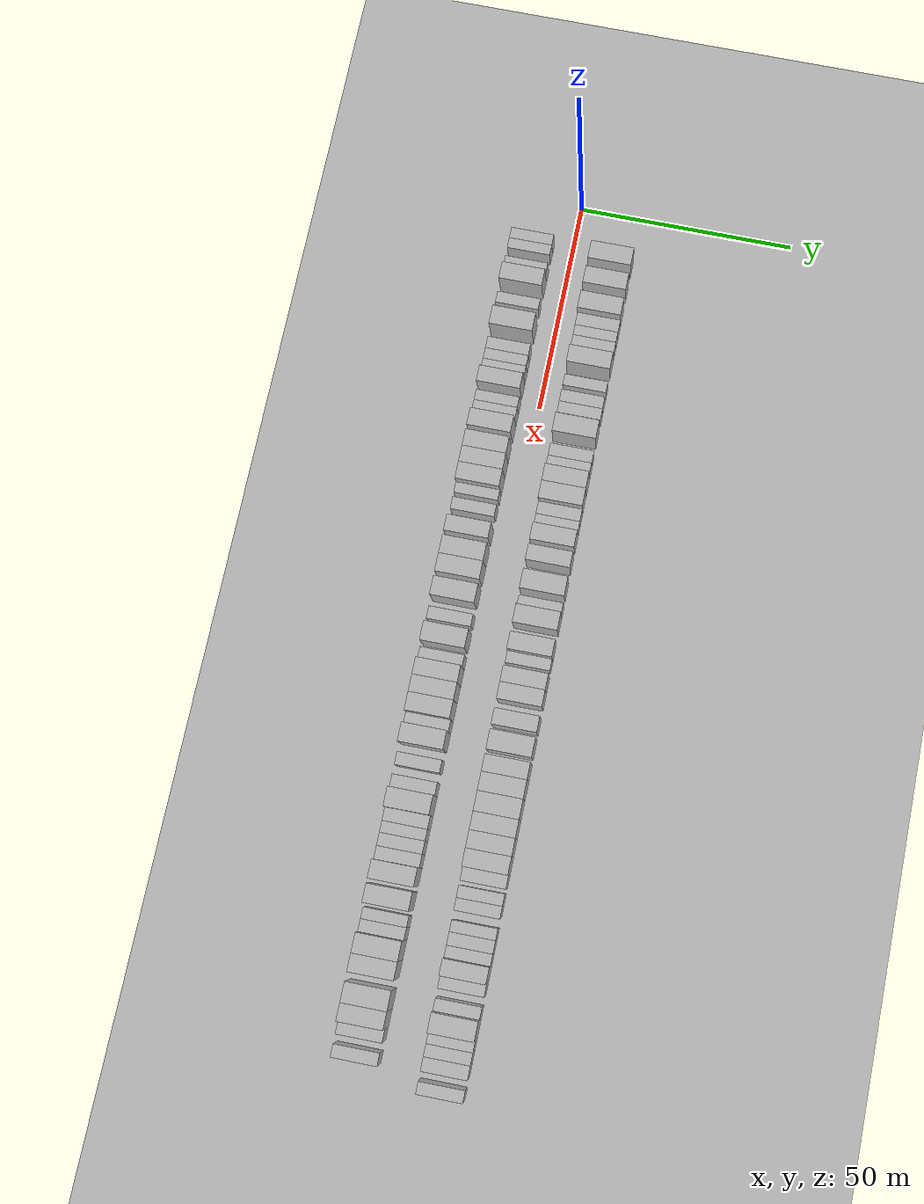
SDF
<?xml version="1.0" encoding="utf-8"?>

<sdf version="1.6">

   <world name="default">

      <gui fullscreen="0">

         <camera name="user_camera">

            <pose>-15 0 4.57585 0 0 0</pose>

            <view_controller>orbit</view_controller>

         </camera>

      </gui>

      <scene>

         <sky>

           <clouds>

             <speed>12</speed>

           </clouds>

         </sky>

         <ambient>0.4 0.4 0.4 1</ambient>

         <background>0.7 0.7 0.7 1</background>

         <shadows>1</shadows>

      </scene>

      <gravity>0 0 -9.8066</gravity>

      <magnetic_field>6e-06 2.3e-05 -4.2e-05</magnetic_field>

      <physics default="0" name="default_physics" type="ode">

         <ode>

            <solver>

               <type>quick</type>

               <iters>10</iters>

               <sor>1.0</sor>

               <use_dynamic_moi_rescaling>0</use_dynamic_moi_rescaling>

            </solver>

            <constraints>

               <cfm>0</cfm>

               <erp>0.2</erp>

               <contact_max_correcting_vel>100</contact_max_correcting_vel>

               <contact_surface_layer>0.001</contact_surface_layer>

            </constraints>

         </ode>

         <max_step_size>0.004</max_step_size>

         <real_time_factor>1</real_time_factor>

         <real_time_update_rate>250</real_time_update_rate>

      </physics>

      <light name="sun" type="directional">

         <cast_shadows>1</cast_shadows>

         <pose>0 0 10 0 0 0</pose>

         <diffuse>0.8 0.8 0.8 1</diffuse>

         <specular>0.2 0.2 0.2 1</specular>

         <attenuation>

            <range>1000</range>

            <constant>0.9</constant>

            <linear>0.01</linear>

            <quadratic>0.001</quadratic>

         </attenuation>

         <direction>-0.5 0.1 -0.9</direction>

      </light>

      <include>

         <name>ground_plane_1</name>

         <uri>model://HANNAS_ground_plane</uri>

         <pose>0 0 0  0 0 0</pose>

      </include>

      <include>

         <name>ground_plane_2</name>

         <uri>model://HANNAS_ground_plane</uri>

         <pose>100 0 0  0 0 0</pose>

      </include>

      <model name="building_1">

         <static>1</static>

         <pose frame="">13.1404 9.5000 0 0.000000 0.000000 1.570796</pose>

         <link name="link">

            <pose frame="">0 0 4.50 0 0 0</pose>

            <collision name="collision">

               <geometry>

                  <box>

                     <size>10.0000 4.2808 9.0000</size>

                  </box>

               </geometry>

               <max_contacts>10</max_contacts>

               <surface>

                  <contact>

                     <ode/>

                  </contact>

                  <bounce/>

                  <friction>

                     <torsional>

                        <ode/>

                     </torsional>

                     <ode/>

                  </friction>

               </surface>

            </collision>

            <visual name="visual">

               <cast_shadows>0</cast_shadows>

               <geometry>

                  <box>

                     <size>10.0000 4.2808 9.0000</size>

                  </box>

               </geometry>

               <material>

                  <script>

                     <uri>model://HANNAS_wall/materials/scripts</uri>

                     <uri>model://HANNAS_wall/materials/textures</uri>

                     <name>vrc/HANNAS_wall</name>

                  </script>

               </material>

            </visual>

            <self_collide>0</self_collide>

            <enable_wind>0</enable_wind>

            <kinematic>0</kinematic>

         </link>

      </model>

      <model name="building_2">

         <static>1</static>

         <pose frame="">19.3093 9.5000 0 0.000000 0.000000 1.570796</pose>

         <link name="link">

            <pose frame="">0 0 4.50 0 0 0</pose>

            <collision name="collision">

               <geometry>

                  <box>

                     <size>10.0000 4.0569 9.0000</size>

                  </box>

               </geometry>

               <max_contacts>10</max_contacts>

               <surface>

                  <contact>

                     <ode/>

                  </contact>

                  <bounce/>

                  <friction>

                     <torsional>

                        <ode/>

                     </torsional>

                     <ode/>

                  </friction>

               </surface>

            </collision>

            <visual name="visual">

               <cast_shadows>0</cast_shadows>

               <geometry>

                  <box>

                     <size>10.0000 4.0569 9.0000</size>

                  </box>

               </geometry>

               <material>

                  <script>

                     <uri>model://HANNAS_wall/materials/scripts</uri>

                     <uri>model://HANNAS_wall/materials/textures</uri>

                     <name>vrc/HANNAS_wall</name>

                  </script>

               </material>

            </visual>

            <self_collide>0</self_collide>

            <enable_wind>0</enable_wind>

            <kinematic>0</kinematic>

         </link>

      </model>

      <model name="building_3">

         <static>1</static>

         <pose frame="">25.4504 9.5000 0 0.000000 0.000000 1.570796</pose>

         <link name="link">

            <pose frame="">0 0 4.50 0 0 0</pose>

            <collision name="collision">

               <geometry>

                  <box>

                     <size>10.0000 4.2252 9.0000</size>

                  </box>

               </geometry>

               <max_contacts>10</max_contacts>

               <surface>

                  <contact>

                     <ode/>

                  </contact>

                  <bounce/>

                  <friction>

                     <torsional>

                        <ode/>

                     </torsional>

                     <ode/>

                  </friction>

               </surface>

            </collision>

            <visual name="visual">

               <cast_shadows>0</cast_shadows>

               <geometry>

                  <box>

                     <size>10.0000 4.2252 9.0000</size>

                  </box>

               </geometry>

               <material>

                  <script>

                     <uri>model://HANNAS_wall/materials/scripts</uri>

                     <uri>model://HANNAS_wall/materials/textures</uri>

                     <name>vrc/HANNAS_wall</name>

                  </script>

               </material>

            </visual>

            <self_collide>0</self_collide>

            <enable_wind>0</enable_wind>

            <kinematic>0</kinematic>

         </link>

      </model>

      <model name="building_4">

         <static>1</static>

         <pose frame="">29.0588 9.5000 0 0.000000 0.000000 1.570796</pose>

         <link name="link">

            <pose frame="">0 0 3.00 0 0 0</pose>

            <collision name="collision">

               <geometry>

                  <box>

                     <size>10.0000 2.9917 6.0000</size>

                  </box>

               </geometry>

               <max_contacts>10</max_contacts>

               <surface>

                  <contact>

                     <ode/>

                  </contact>

                  <bounce/>

                  <friction>

                     <torsional>

                        <ode/>

                     </torsional>

                     <ode/>

                  </friction>

               </surface>

            </collision>

            <visual name="visual">

               <cast_shadows>0</cast_shadows>

               <geometry>

                  <box>

                     <size>10.0000 2.9917 6.0000</size>

                  </box>

               </geometry>

               <material>

                  <script>

                     <uri>model://HANNAS_wall/materials/scripts</uri>

                     <uri>model://HANNAS_wall/materials/textures</uri>

                     <name>vrc/HANNAS_wall</name>

                  </script>

               </material>

            </visual>

            <self_collide>0</self_collide>

            <enable_wind>0</enable_wind>

            <kinematic>0</kinematic>

         </link>

      </model>

      <model name="building_5">

         <static>1</static>

         <pose frame="">31.7879 9.5000 0 0.000000 0.000000 1.570796</pose>

         <link name="link">

            <pose frame="">0 0 3.00 0 0 0</pose>

            <collision name="collision">

               <geometry>

                  <box>

                     <size>10.0000 2.4665 6.0000</size>

                  </box>

               </geometry>

               <max_contacts>10</max_contacts>

               <surface>

                  <contact>

                     <ode/>

                  </contact>

                  <bounce/>

                  <friction>

                     <torsional>

                        <ode/>

                     </torsional>

                     <ode/>

                  </friction>

               </surface>

            </collision>

            <visual name="visual">

               <cast_shadows>0</cast_shadows>

               <geometry>

                  <box>

                     <size>10.0000 2.4665 6.0000</size>

                  </box>

               </geometry>

               <material>

                  <script>

                     <uri>model://HANNAS_wall/materials/scripts</uri>

                     <uri>model://HANNAS_wall/materials/textures</uri>

                     <name>vrc/HANNAS_wall</name>

                  </script>

               </material>

            </visual>

            <self_collide>0</self_collide>

            <enable_wind>0</enable_wind>

            <kinematic>0</kinematic>

         </link>

      </model>

      <model name="building_6">

         <static>1</static>

         <pose frame="">34.2926 9.5000 0 0.000000 0.000000 1.570796</pose>

         <link name="link">

            <pose frame="">0 0 3.00 0 0 0</pose>

            <collision name="collision">

               <geometry>

                  <box>

                     <size>10.0000 2.5428 6.0000</size>

                  </box>

               </geometry>

               <max_contacts>10</max_contacts>

               <surface>

                  <contact>

                     <ode/>

                  </contact>

                  <bounce/>

                  <friction>

                     <torsional>

                        <ode/>

                     </torsional>

                     <ode/>

                  </friction>

               </surface>

            </collision>

            <visual name="visual">

               <cast_shadows>0</cast_shadows>

               <geometry>

                  <box>

                     <size>10.0000 2.5428 6.0000</size>

                  </box>

               </geometry>

               <material>

                  <script>

                     <uri>model://HANNAS_wall/materials/scripts</uri>

                     <uri>model://HANNAS_wall/materials/textures</uri>

                     <name>vrc/HANNAS_wall</name>

                  </script>

               </material>

            </visual>

            <self_collide>0</self_collide>

            <enable_wind>0</enable_wind>

            <kinematic>0</kinematic>

         </link>

      </model>

      <model name="building_7">

         <static>1</static>

         <pose frame="">38.5831 9.5000 0 0.000000 0.000000 1.570796</pose>

         <link name="link">

            <pose frame="">0 0 4.50 0 0 0</pose>

            <collision name="collision">

               <geometry>

                  <box>

                     <size>10.0000 4.0381 9.0000</size>

                  </box>

               </geometry>

               <max_contacts>10</max_contacts>

               <surface>

                  <contact>

                     <ode/>

                  </contact>

                  <bounce/>

                  <friction>

                     <torsional>

                        <ode/>

                     </torsional>

                     <ode/>

                  </friction>

               </surface>

            </collision>

            <visual name="visual">

               <cast_shadows>0</cast_shadows>

               <geometry>

                  <box>

                     <size>10.0000 4.0381 9.0000</size>

                  </box>

               </geometry>

               <material>

                  <script>

                     <uri>model://HANNAS_wall/materials/scripts</uri>

                     <uri>model://HANNAS_wall/materials/textures</uri>

                     <name>vrc/HANNAS_wall</name>

                  </script>

               </material>

            </visual>

            <self_collide>0</self_collide>

            <enable_wind>0</enable_wind>

            <kinematic>0</kinematic>

         </link>

      </model>

      <model name="building_8">

         <static>1</static>

         <pose frame="">43.9458 9.5000 0 0.000000 0.000000 1.570796</pose>

         <link name="link">

            <pose frame="">0 0 3.00 0 0 0</pose>

            <collision name="collision">

               <geometry>

                  <box>

                     <size>10.0000 2.6873 6.0000</size>

                  </box>

               </geometry>

               <max_contacts>10</max_contacts>

               <surface>

                  <contact>

                     <ode/>

                  </contact>

                  <bounce/>

                  <friction>

                     <torsional>

                        <ode/>

                     </torsional>

                     <ode/>

                  </friction>

               </surface>

            </collision>

            <visual name="visual">

               <cast_shadows>0</cast_shadows>

               <geometry>

                  <box>

                     <size>10.0000 2.6873 6.0000</size>

                  </box>

               </geometry>

               <material>

                  <script>

                     <uri>model://HANNAS_wall/materials/scripts</uri>

                     <uri>model://HANNAS_wall/materials/textures</uri>

                     <name>vrc/HANNAS_wall</name>

                  </script>

               </material>

            </visual>

            <self_collide>0</self_collide>

            <enable_wind>0</enable_wind>

            <kinematic>0</kinematic>

         </link>

      </model>

      <model name="building_9">

         <static>1</static>

         <pose frame="">47.7086 9.5000 0 0.000000 0.000000 1.570796</pose>

         <link name="link">

            <pose frame="">0 0 3.00 0 0 0</pose>

            <collision name="collision">

               <geometry>

                  <box>

                     <size>10.0000 2.8384 6.0000</size>

                  </box>

               </geometry>

               <max_contacts>10</max_contacts>

               <surface>

                  <contact>

                     <ode/>

                  </contact>

                  <bounce/>

                  <friction>

                     <torsional>

                        <ode/>

                     </torsional>

                     <ode/>

                  </friction>

               </surface>

            </collision>

            <visual name="visual">

               <cast_shadows>0</cast_shadows>

               <geometry>

                  <box>

                     <size>10.0000 2.8384 6.0000</size>

                  </box>

               </geometry>

               <material>

                  <script>

                     <uri>model://HANNAS_wall/materials/scripts</uri>

                     <uri>model://HANNAS_wall/materials/textures</uri>

                     <name>vrc/HANNAS_wall</name>

                  </script>

               </material>

            </visual>

            <self_collide>0</self_collide>

            <enable_wind>0</enable_wind>

            <kinematic>0</kinematic>

         </link>

      </model>

      <model name="building_10">

         <static>1</static>

         <pose frame="">50.4885 9.5000 0 0.000000 0.000000 1.570796</pose>

         <link name="link">

            <pose frame="">0 0 3.00 0 0 0</pose>

            <collision name="collision">

               <geometry>

                  <box>

                     <size>10.0000 2.7214 6.0000</size>

                  </box>

               </geometry>

               <max_contacts>10</max_contacts>

               <surface>

                  <contact>

                     <ode/>

                  </contact>

                  <bounce/>

                  <friction>

                     <torsional>

                        <ode/>

                     </torsional>

                     <ode/>

                  </friction>

               </surface>

            </collision>

            <visual name="visual">

               <cast_shadows>0</cast_shadows>

               <geometry>

                  <box>

                     <size>10.0000 2.7214 6.0000</size>

                  </box>

               </geometry>

               <material>

                  <script>

                     <uri>model://HANNAS_wall/materials/scripts</uri>

                     <uri>model://HANNAS_wall/materials/textures</uri>

                     <name>vrc/HANNAS_wall</name>

                  </script>

               </material>

            </visual>

            <self_collide>0</self_collide>

            <enable_wind>0</enable_wind>

            <kinematic>0</kinematic>

         </link>

      </model>

      <model name="building_11">

         <static>1</static>

         <pose frame="">55.0271 9.5000 0 0.000000 0.000000 1.570796</pose>

         <link name="link">

            <pose frame="">0 0 4.50 0 0 0</pose>

            <collision name="collision">

               <geometry>

                  <box>

                     <size>10.0000 4.3558 9.0000</size>

                  </box>

               </geometry>

               <max_contacts>10</max_contacts>

               <surface>

                  <contact>

                     <ode/>

                  </contact>

                  <bounce/>

                  <friction>

                     <torsional>

                        <ode/>

                     </torsional>

                     <ode/>

                  </friction>

               </surface>

            </collision>

            <visual name="visual">

               <cast_shadows>0</cast_shadows>

               <geometry>

                  <box>

                     <size>10.0000 4.3558 9.0000</size>

                  </box>

               </geometry>

               <material>

                  <script>

                     <uri>model://HANNAS_wall/materials/scripts</uri>

                     <uri>model://HANNAS_wall/materials/textures</uri>

                     <name>vrc/HANNAS_wall</name>

                  </script>

               </material>

            </visual>

            <self_collide>0</self_collide>

            <enable_wind>0</enable_wind>

            <kinematic>0</kinematic>

         </link>

      </model>

      <model name="building_12">

         <static>1</static>

         <pose frame="">60.6485 9.5000 0 0.000000 0.000000 1.570796</pose>

         <link name="link">

            <pose frame="">0 0 3.00 0 0 0</pose>

            <collision name="collision">

               <geometry>

                  <box>

                     <size>10.0000 2.8870 6.0000</size>

                  </box>

               </geometry>

               <max_contacts>10</max_contacts>

               <surface>

                  <contact>

                     <ode/>

                  </contact>

                  <bounce/>

                  <friction>

                     <torsional>

                        <ode/>

                     </torsional>

                     <ode/>

                  </friction>

               </surface>

            </collision>

            <visual name="visual">

               <cast_shadows>0</cast_shadows>

               <geometry>

                  <box>

                     <size>10.0000 2.8870 6.0000</size>

                  </box>

               </geometry>

               <material>

                  <script>

                     <uri>model://HANNAS_wall/materials/scripts</uri>

                     <uri>model://HANNAS_wall/materials/textures</uri>

                     <name>vrc/HANNAS_wall</name>

                  </script>

               </material>

            </visual>

            <self_collide>0</self_collide>

            <enable_wind>0</enable_wind>

            <kinematic>0</kinematic>

         </link>

      </model>

      <model name="building_13">

         <static>1</static>

         <pose frame="">63.5097 9.5000 0 0.000000 0.000000 1.570796</pose>

         <link name="link">

            <pose frame="">0 0 3.00 0 0 0</pose>

            <collision name="collision">

               <geometry>

                  <box>

                     <size>10.0000 2.8355 6.0000</size>

                  </box>

               </geometry>

               <max_contacts>10</max_contacts>

               <surface>

                  <contact>

                     <ode/>

                  </contact>

                  <bounce/>

                  <friction>

                     <torsional>

                        <ode/>

                     </torsional>

                     <ode/>

                  </friction>

               </surface>

            </collision>

            <visual name="visual">

               <cast_shadows>0</cast_shadows>

               <geometry>

                  <box>

                     <size>10.0000 2.8355 6.0000</size>

                  </box>

               </geometry>

               <material>

                  <script>

                     <uri>model://HANNAS_wall/materials/scripts</uri>

                     <uri>model://HANNAS_wall/materials/textures</uri>

                     <name>vrc/HANNAS_wall</name>

                  </script>

               </material>

            </visual>

            <self_collide>0</self_collide>

            <enable_wind>0</enable_wind>

            <kinematic>0</kinematic>

         </link>

      </model>

      <model name="building_14">

         <static>1</static>

         <pose frame="">66.8850 9.5000 0 0.000000 0.000000 1.570796</pose>

         <link name="link">

            <pose frame="">0 0 4.50 0 0 0</pose>

            <collision name="collision">

               <geometry>

                  <box>

                     <size>10.0000 3.9152 9.0000</size>

                  </box>

               </geometry>

               <max_contacts>10</max_contacts>

               <surface>

                  <contact>

                     <ode/>

                  </contact>

                  <bounce/>

                  <friction>

                     <torsional>

                        <ode/>

                     </torsional>

                     <ode/>

                  </friction>

               </surface>

            </collision>

            <visual name="visual">

               <cast_shadows>0</cast_shadows>

               <geometry>

                  <box>

                     <size>10.0000 3.9152 9.0000</size>

                  </box>

               </geometry>

               <material>

                  <script>

                     <uri>model://HANNAS_wall/materials/scripts</uri>

                     <uri>model://HANNAS_wall/materials/textures</uri>

                     <name>vrc/HANNAS_wall</name>

                  </script>

               </material>

            </visual>

            <self_collide>0</self_collide>

            <enable_wind>0</enable_wind>

            <kinematic>0</kinematic>

         </link>

      </model>

      <model name="building_15">

         <static>1</static>

         <pose frame="">70.8978 9.5000 0 0.000000 0.000000 1.570796</pose>

         <link name="link">

            <pose frame="">0 0 4.50 0 0 0</pose>

            <collision name="collision">

               <geometry>

                  <box>

                     <size>10.0000 4.1103 9.0000</size>

                  </box>

               </geometry>

               <max_contacts>10</max_contacts>

               <surface>

                  <contact>

                     <ode/>

                  </contact>

                  <bounce/>

                  <friction>

                     <torsional>

                        <ode/>

                     </torsional>

                     <ode/>

                  </friction>

               </surface>

            </collision>

            <visual name="visual">

               <cast_shadows>0</cast_shadows>

               <geometry>

                  <box>

                     <size>10.0000 4.1103 9.0000</size>

                  </box>

               </geometry>

               <material>

                  <script>

                     <uri>model://HANNAS_wall/materials/scripts</uri>

                     <uri>model://HANNAS_wall/materials/textures</uri>

                     <name>vrc/HANNAS_wall</name>

                  </script>

               </material>

            </visual>

            <self_collide>0</self_collide>

            <enable_wind>0</enable_wind>

            <kinematic>0</kinematic>

         </link>

      </model>

      <model name="building_16">

         <static>1</static>

         <pose frame="">74.4042 9.5000 0 0.000000 0.000000 1.570796</pose>

         <link name="link">

            <pose frame="">0 0 3.00 0 0 0</pose>

            <collision name="collision">

               <geometry>

                  <box>

                     <size>10.0000 2.9024 6.0000</size>

                  </box>

               </geometry>

               <max_contacts>10</max_contacts>

               <surface>

                  <contact>

                     <ode/>

                  </contact>

                  <bounce/>

                  <friction>

                     <torsional>

                        <ode/>

                     </torsional>

                     <ode/>

                  </friction>

               </surface>

            </collision>

            <visual name="visual">

               <cast_shadows>0</cast_shadows>

               <geometry>

                  <box>

                     <size>10.0000 2.9024 6.0000</size>

                  </box>

               </geometry>

               <material>

                  <script>

                     <uri>model://HANNAS_wall/materials/scripts</uri>

                     <uri>model://HANNAS_wall/materials/textures</uri>

                     <name>vrc/HANNAS_wall</name>

                  </script>

               </material>

            </visual>

            <self_collide>0</self_collide>

            <enable_wind>0</enable_wind>

            <kinematic>0</kinematic>

         </link>

      </model>

      <model name="building_17">

         <static>1</static>

         <pose frame="">77.2181 9.5000 0 0.000000 0.000000 1.570796</pose>

         <link name="link">

            <pose frame="">0 0 3.00 0 0 0</pose>

            <collision name="collision">

               <geometry>

                  <box>

                     <size>10.0000 2.7256 6.0000</size>

                  </box>

               </geometry>

               <max_contacts>10</max_contacts>

               <surface>

                  <contact>

                     <ode/>

                  </contact>

                  <bounce/>

                  <friction>

                     <torsional>

                        <ode/>

                     </torsional>

                     <ode/>

                  </friction>

               </surface>

            </collision>

            <visual name="visual">

               <cast_shadows>0</cast_shadows>

               <geometry>

                  <box>

                     <size>10.0000 2.7256 6.0000</size>

                  </box>

               </geometry>

               <material>

                  <script>

                     <uri>model://HANNAS_wall/materials/scripts</uri>

                     <uri>model://HANNAS_wall/materials/textures</uri>

                     <name>vrc/HANNAS_wall</name>

                  </script>

               </material>

            </visual>

            <self_collide>0</self_collide>

            <enable_wind>0</enable_wind>

            <kinematic>0</kinematic>

         </link>

      </model>

      <model name="building_18">

         <static>1</static>

         <pose frame="">80.5503 9.5000 0 0.000000 0.000000 1.570796</pose>

         <link name="link">

            <pose frame="">0 0 4.50 0 0 0</pose>

            <collision name="collision">

               <geometry>

                  <box>

                     <size>10.0000 3.9388 9.0000</size>

                  </box>

               </geometry>

               <max_contacts>10</max_contacts>

               <surface>

                  <contact>

                     <ode/>

                  </contact>

                  <bounce/>

                  <friction>

                     <torsional>

                        <ode/>

                     </torsional>

                     <ode/>

                  </friction>

               </surface>

            </collision>

            <visual name="visual">

               <cast_shadows>0</cast_shadows>

               <geometry>

                  <box>

                     <size>10.0000 3.9388 9.0000</size>

                  </box>

               </geometry>

               <material>

                  <script>

                     <uri>model://HANNAS_wall/materials/scripts</uri>

                     <uri>model://HANNAS_wall/materials/textures</uri>

                     <name>vrc/HANNAS_wall</name>

                  </script>

               </material>

            </visual>

            <self_collide>0</self_collide>

            <enable_wind>0</enable_wind>

            <kinematic>0</kinematic>

         </link>

      </model>

      <model name="building_19">

         <static>1</static>

         <pose frame="">85.3523 9.5000 0 0.000000 0.000000 1.570796</pose>

         <link name="link">

            <pose frame="">0 0 4.50 0 0 0</pose>

            <collision name="collision">

               <geometry>

                  <box>

                     <size>10.0000 3.6652 9.0000</size>

                  </box>

               </geometry>

               <max_contacts>10</max_contacts>

               <surface>

                  <contact>

                     <ode/>

                  </contact>

                  <bounce/>

                  <friction>

                     <torsional>

                        <ode/>

                     </torsional>

                     <ode/>

                  </friction>

               </surface>

            </collision>

            <visual name="visual">

               <cast_shadows>0</cast_shadows>

               <geometry>

                  <box>

                     <size>10.0000 3.6652 9.0000</size>

                  </box>

               </geometry>

               <material>

                  <script>

                     <uri>model://HANNAS_wall/materials/scripts</uri>

                     <uri>model://HANNAS_wall/materials/textures</uri>

                     <name>vrc/HANNAS_wall</name>

                  </script>

               </material>

            </visual>

            <self_collide>0</self_collide>

            <enable_wind>0</enable_wind>

            <kinematic>0</kinematic>

         </link>

      </model>

      <model name="building_20">

         <static>1</static>

         <pose frame="">91.4094 9.5000 0 0.000000 0.000000 1.570796</pose>

         <link name="link">

            <pose frame="">0 0 4.50 0 0 0</pose>

            <collision name="collision">

               <geometry>

                  <box>

                     <size>10.0000 4.4489 9.0000</size>

                  </box>

               </geometry>

               <max_contacts>10</max_contacts>

               <surface>

                  <contact>

                     <ode/>

                  </contact>

                  <bounce/>

                  <friction>

                     <torsional>

                        <ode/>

                     </torsional>

                     <ode/>

                  </friction>

               </surface>

            </collision>

            <visual name="visual">

               <cast_shadows>0</cast_shadows>

               <geometry>

                  <box>

                     <size>10.0000 4.4489 9.0000</size>

                  </box>

               </geometry>

               <material>

                  <script>

                     <uri>model://HANNAS_wall/materials/scripts</uri>

                     <uri>model://HANNAS_wall/materials/textures</uri>

                     <name>vrc/HANNAS_wall</name>

                  </script>

               </material>

            </visual>

            <self_collide>0</self_collide>

            <enable_wind>0</enable_wind>

            <kinematic>0</kinematic>

         </link>

      </model>

      <model name="building_21">

         <static>1</static>

         <pose frame="">95.9213 9.5000 0 0.000000 0.000000 1.570796</pose>

         <link name="link">

            <pose frame="">0 0 3.00 0 0 0</pose>

            <collision name="collision">

               <geometry>

                  <box>

                     <size>10.0000 2.5750 6.0000</size>

                  </box>

               </geometry>

               <max_contacts>10</max_contacts>

               <surface>

                  <contact>

                     <ode/>

                  </contact>

                  <bounce/>

                  <friction>

                     <torsional>

                        <ode/>

                     </torsional>

                     <ode/>

                  </friction>

               </surface>

            </collision>

            <visual name="visual">

               <cast_shadows>0</cast_shadows>

               <geometry>

                  <box>

                     <size>10.0000 2.5750 6.0000</size>

                  </box>

               </geometry>

               <material>

                  <script>

                     <uri>model://HANNAS_wall/materials/scripts</uri>

                     <uri>model://HANNAS_wall/materials/textures</uri>

                     <name>vrc/HANNAS_wall</name>

                  </script>

               </material>

            </visual>

            <self_collide>0</self_collide>

            <enable_wind>0</enable_wind>

            <kinematic>0</kinematic>

         </link>

      </model>

      <model name="building_22">

         <static>1</static>

         <pose frame="">99.3051 9.5000 0 0.000000 0.000000 1.570796</pose>

         <link name="link">

            <pose frame="">0 0 4.50 0 0 0</pose>

            <collision name="collision">

               <geometry>

                  <box>

                     <size>10.0000 4.1926 9.0000</size>

                  </box>

               </geometry>

               <max_contacts>10</max_contacts>

               <surface>

                  <contact>

                     <ode/>

                  </contact>

                  <bounce/>

                  <friction>

                     <torsional>

                        <ode/>

                     </torsional>

                     <ode/>

                  </friction>

               </surface>

            </collision>

            <visual name="visual">

               <cast_shadows>0</cast_shadows>

               <geometry>

                  <box>

                     <size>10.0000 4.1926 9.0000</size>

                  </box>

               </geometry>

               <material>

                  <script>

                     <uri>model://HANNAS_wall/materials/scripts</uri>

                     <uri>model://HANNAS_wall/materials/textures</uri>

                     <name>vrc/HANNAS_wall</name>

                  </script>

               </material>

            </visual>

            <self_collide>0</self_collide>

            <enable_wind>0</enable_wind>

            <kinematic>0</kinematic>

         </link>

      </model>

      <model name="building_23">

         <static>1</static>

         <pose frame="">105.3759 9.5000 0 0.000000 0.000000 1.570796</pose>

         <link name="link">

            <pose frame="">0 0 4.50 0 0 0</pose>

            <collision name="collision">

               <geometry>

                  <box>

                     <size>10.0000 3.9490 9.0000</size>

                  </box>

               </geometry>

               <max_contacts>10</max_contacts>

               <surface>

                  <contact>

                     <ode/>

                  </contact>

                  <bounce/>

                  <friction>

                     <torsional>

                        <ode/>

                     </torsional>

                     <ode/>

                  </friction>

               </surface>

            </collision>

            <visual name="visual">

               <cast_shadows>0</cast_shadows>

               <geometry>

                  <box>

                     <size>10.0000 3.9490 9.0000</size>

                  </box>

               </geometry>

               <material>

                  <script>

                     <uri>model://HANNAS_wall/materials/scripts</uri>

                     <uri>model://HANNAS_wall/materials/textures</uri>

                     <name>vrc/HANNAS_wall</name>

                  </script>

               </material>

            </visual>

            <self_collide>0</self_collide>

            <enable_wind>0</enable_wind>

            <kinematic>0</kinematic>

         </link>

      </model>

      <model name="building_24">

         <static>1</static>

         <pose frame="">108.6843 9.5000 0 0.000000 0.000000 1.570796</pose>

         <link name="link">

            <pose frame="">0 0 3.00 0 0 0</pose>

            <collision name="collision">

               <geometry>

                  <box>

                     <size>10.0000 2.6677 6.0000</size>

                  </box>

               </geometry>

               <max_contacts>10</max_contacts>

               <surface>

                  <contact>

                     <ode/>

                  </contact>

                  <bounce/>

                  <friction>

                     <torsional>

                        <ode/>

                     </torsional>

                     <ode/>

                  </friction>

               </surface>

            </collision>

            <visual name="visual">

               <cast_shadows>0</cast_shadows>

               <geometry>

                  <box>

                     <size>10.0000 2.6677 6.0000</size>

                  </box>

               </geometry>

               <material>

                  <script>

                     <uri>model://HANNAS_wall/materials/scripts</uri>

                     <uri>model://HANNAS_wall/materials/textures</uri>

                     <name>vrc/HANNAS_wall</name>

                  </script>

               </material>

            </visual>

            <self_collide>0</self_collide>

            <enable_wind>0</enable_wind>

            <kinematic>0</kinematic>

         </link>

      </model>

      <model name="building_25">

         <static>1</static>

         <pose frame="">112.8357 9.5000 0 0.000000 0.000000 1.570796</pose>

         <link name="link">

            <pose frame="">0 0 4.50 0 0 0</pose>

            <collision name="collision">

               <geometry>

                  <box>

                     <size>10.0000 3.6351 9.0000</size>

                  </box>

               </geometry>

               <max_contacts>10</max_contacts>

               <surface>

                  <contact>

                     <ode/>

                  </contact>

                  <bounce/>

                  <friction>

                     <torsional>

                        <ode/>

                     </torsional>

                     <ode/>

                  </friction>

               </surface>

            </collision>

            <visual name="visual">

               <cast_shadows>0</cast_shadows>

               <geometry>

                  <box>

                     <size>10.0000 3.6351 9.0000</size>

                  </box>

               </geometry>

               <material>

                  <script>

                     <uri>model://HANNAS_wall/materials/scripts</uri>

                     <uri>model://HANNAS_wall/materials/textures</uri>

                     <name>vrc/HANNAS_wall</name>

                  </script>

               </material>

            </visual>

            <self_collide>0</self_collide>

            <enable_wind>0</enable_wind>

            <kinematic>0</kinematic>

         </link>

      </model>

      <model name="building_26">

         <static>1</static>

         <pose frame="">116.5429 9.5000 0 0.000000 0.000000 1.570796</pose>

         <link name="link">

            <pose frame="">0 0 4.50 0 0 0</pose>

            <collision name="collision">

               <geometry>

                  <box>

                     <size>10.0000 3.7794 9.0000</size>

                  </box>

               </geometry>

               <max_contacts>10</max_contacts>

               <surface>

                  <contact>

                     <ode/>

                  </contact>

                  <bounce/>

                  <friction>

                     <torsional>

                        <ode/>

                     </torsional>

                     <ode/>

                  </friction>

               </surface>

            </collision>

            <visual name="visual">

               <cast_shadows>0</cast_shadows>

               <geometry>

                  <box>

                     <size>10.0000 3.7794 9.0000</size>

                  </box>

               </geometry>

               <material>

                  <script>

                     <uri>model://HANNAS_wall/materials/scripts</uri>

                     <uri>model://HANNAS_wall/materials/textures</uri>

                     <name>vrc/HANNAS_wall</name>

                  </script>

               </material>

            </visual>

            <self_collide>0</self_collide>

            <enable_wind>0</enable_wind>

            <kinematic>0</kinematic>

         </link>

      </model>

      <model name="building_27">

         <static>1</static>

         <pose frame="">122.2377 9.5000 0 0.000000 0.000000 1.570796</pose>

         <link name="link">

            <pose frame="">0 0 4.50 0 0 0</pose>

            <collision name="collision">

               <geometry>

                  <box>

                     <size>10.0000 3.6102 9.0000</size>

                  </box>

               </geometry>

               <max_contacts>10</max_contacts>

               <surface>

                  <contact>

                     <ode/>

                  </contact>

                  <bounce/>

                  <friction>

                     <torsional>

                        <ode/>

                     </torsional>

                     <ode/>

                  </friction>

               </surface>

            </collision>

            <visual name="visual">

               <cast_shadows>0</cast_shadows>

               <geometry>

                  <box>

                     <size>10.0000 3.6102 9.0000</size>

                  </box>

               </geometry>

               <material>

                  <script>

                     <uri>model://HANNAS_wall/materials/scripts</uri>

                     <uri>model://HANNAS_wall/materials/textures</uri>

                     <name>vrc/HANNAS_wall</name>

                  </script>

               </material>

            </visual>

            <self_collide>0</self_collide>

            <enable_wind>0</enable_wind>

            <kinematic>0</kinematic>

         </link>

      </model>

      <model name="building_28">

         <static>1</static>

         <pose frame="">127.2770 9.5000 0 0.000000 0.000000 1.570796</pose>

         <link name="link">

            <pose frame="">0 0 4.50 0 0 0</pose>

            <collision name="collision">

               <geometry>

                  <box>

                     <size>10.0000 4.4685 9.0000</size>

                  </box>

               </geometry>

               <max_contacts>10</max_contacts>

               <surface>

                  <contact>

                     <ode/>

                  </contact>

                  <bounce/>

                  <friction>

                     <torsional>

                        <ode/>

                     </torsional>

                     <ode/>

                  </friction>

               </surface>

            </collision>

            <visual name="visual">

               <cast_shadows>0</cast_shadows>

               <geometry>

                  <box>

                     <size>10.0000 4.4685 9.0000</size>

                  </box>

               </geometry>

               <material>

                  <script>

                     <uri>model://HANNAS_wall/materials/scripts</uri>

                     <uri>model://HANNAS_wall/materials/textures</uri>

                     <name>vrc/HANNAS_wall</name>

                  </script>

               </material>

            </visual>

            <self_collide>0</self_collide>

            <enable_wind>0</enable_wind>

            <kinematic>0</kinematic>

         </link>

      </model>

      <model name="building_29">

         <static>1</static>

         <pose frame="">132.4076 9.5000 0 0.000000 0.000000 1.570796</pose>

         <link name="link">

            <pose frame="">0 0 4.50 0 0 0</pose>

            <collision name="collision">

               <geometry>

                  <box>

                     <size>10.0000 3.7927 9.0000</size>

                  </box>

               </geometry>

               <max_contacts>10</max_contacts>

               <surface>

                  <contact>

                     <ode/>

                  </contact>

                  <bounce/>

                  <friction>

                     <torsional>

                        <ode/>

                     </torsional>

                     <ode/>

                  </friction>

               </surface>

            </collision>

            <visual name="visual">

               <cast_shadows>0</cast_shadows>

               <geometry>

                  <box>

                     <size>10.0000 3.7927 9.0000</size>

                  </box>

               </geometry>

               <material>

                  <script>

                     <uri>model://HANNAS_wall/materials/scripts</uri>

                     <uri>model://HANNAS_wall/materials/textures</uri>

                     <name>vrc/HANNAS_wall</name>

                  </script>

               </material>

            </visual>

            <self_collide>0</self_collide>

            <enable_wind>0</enable_wind>

            <kinematic>0</kinematic>

         </link>

      </model>

      <model name="building_30">

         <static>1</static>

         <pose frame="">136.3838 9.5000 0 0.000000 0.000000 1.570796</pose>

         <link name="link">

            <pose frame="">0 0 4.50 0 0 0</pose>

            <collision name="collision">

               <geometry>

                  <box>

                     <size>10.0000 4.1597 9.0000</size>

                  </box>

               </geometry>

               <max_contacts>10</max_contacts>

               <surface>

                  <contact>

                     <ode/>

                  </contact>

                  <bounce/>

                  <friction>

                     <torsional>

                        <ode/>

                     </torsional>

                     <ode/>

                  </friction>

               </surface>

            </collision>

            <visual name="visual">

               <cast_shadows>0</cast_shadows>

               <geometry>

                  <box>

                     <size>10.0000 4.1597 9.0000</size>

                  </box>

               </geometry>

               <material>

                  <script>

                     <uri>model://HANNAS_wall/materials/scripts</uri>

                     <uri>model://HANNAS_wall/materials/textures</uri>

                     <name>vrc/HANNAS_wall</name>

                  </script>

               </material>

            </visual>

            <self_collide>0</self_collide>

            <enable_wind>0</enable_wind>

            <kinematic>0</kinematic>

         </link>

      </model>

      <model name="building_31">

         <static>1</static>

         <pose frame="">140.6726 9.5000 0 0.000000 0.000000 1.570796</pose>

         <link name="link">

            <pose frame="">0 0 4.50 0 0 0</pose>

            <collision name="collision">

               <geometry>

                  <box>

                     <size>10.0000 4.4179 9.0000</size>

                  </box>

               </geometry>

               <max_contacts>10</max_contacts>

               <surface>

                  <contact>

                     <ode/>

                  </contact>

                  <bounce/>

                  <friction>

                     <torsional>

                        <ode/>

                     </torsional>

                     <ode/>

                  </friction>

               </surface>

            </collision>

            <visual name="visual">

               <cast_shadows>0</cast_shadows>

               <geometry>

                  <box>

                     <size>10.0000 4.4179 9.0000</size>

                  </box>

               </geometry>

               <material>

                  <script>

                     <uri>model://HANNAS_wall/materials/scripts</uri>

                     <uri>model://HANNAS_wall/materials/textures</uri>

                     <name>vrc/HANNAS_wall</name>

                  </script>

               </material>

            </visual>

            <self_collide>0</self_collide>

            <enable_wind>0</enable_wind>

            <kinematic>0</kinematic>

         </link>

      </model>

      <model name="building_32">

         <static>1</static>

         <pose frame="">144.8683 9.5000 0 0.000000 0.000000 1.570796</pose>

         <link name="link">

            <pose frame="">0 0 4.50 0 0 0</pose>

            <collision name="collision">

               <geometry>

                  <box>

                     <size>10.0000 3.9735 9.0000</size>

                  </box>

               </geometry>

               <max_contacts>10</max_contacts>

               <surface>

                  <contact>

                     <ode/>

                  </contact>

                  <bounce/>

                  <friction>

                     <torsional>

                        <ode/>

                     </torsional>

                     <ode/>

                  </friction>

               </surface>

            </collision>

            <visual name="visual">

               <cast_shadows>0</cast_shadows>

               <geometry>

                  <box>

                     <size>10.0000 3.9735 9.0000</size>

                  </box>

               </geometry>

               <material>

                  <script>

                     <uri>model://HANNAS_wall/materials/scripts</uri>

                     <uri>model://HANNAS_wall/materials/textures</uri>

                     <name>vrc/HANNAS_wall</name>

                  </script>

               </material>

            </visual>

            <self_collide>0</self_collide>

            <enable_wind>0</enable_wind>

            <kinematic>0</kinematic>

         </link>

      </model>

      <model name="building_33">

         <static>1</static>

         <pose frame="">148.8022 9.5000 0 0.000000 0.000000 1.570796</pose>

         <link name="link">

            <pose frame="">0 0 4.50 0 0 0</pose>

            <collision name="collision">

               <geometry>

                  <box>

                     <size>10.0000 3.8945 9.0000</size>

                  </box>

               </geometry>

               <max_contacts>10</max_contacts>

               <surface>

                  <contact>

                     <ode/>

                  </contact>

                  <bounce/>

                  <friction>

                     <torsional>

                        <ode/>

                     </torsional>

                     <ode/>

                  </friction>

               </surface>

            </collision>

            <visual name="visual">

               <cast_shadows>0</cast_shadows>

               <geometry>

                  <box>

                     <size>10.0000 3.8945 9.0000</size>

                  </box>

               </geometry>

               <material>

                  <script>

                     <uri>model://HANNAS_wall/materials/scripts</uri>

                     <uri>model://HANNAS_wall/materials/textures</uri>

                     <name>vrc/HANNAS_wall</name>

                  </script>

               </material>

            </visual>

            <self_collide>0</self_collide>

            <enable_wind>0</enable_wind>

            <kinematic>0</kinematic>

         </link>

      </model>

      <model name="building_34">

         <static>1</static>

         <pose frame="">152.7187 9.5000 0 0.000000 0.000000 1.570796</pose>

         <link name="link">

            <pose frame="">0 0 4.50 0 0 0</pose>

            <collision name="collision">

               <geometry>

                  <box>

                     <size>10.0000 3.9385 9.0000</size>

                  </box>

               </geometry>

               <max_contacts>10</max_contacts>

               <surface>

                  <contact>

                     <ode/>

                  </contact>

                  <bounce/>

                  <friction>

                     <torsional>

                        <ode/>

                     </torsional>

                     <ode/>

                  </friction>

               </surface>

            </collision>

            <visual name="visual">

               <cast_shadows>0</cast_shadows>

               <geometry>

                  <box>

                     <size>10.0000 3.9385 9.0000</size>

                  </box>

               </geometry>

               <material>

                  <script>

                     <uri>model://HANNAS_wall/materials/scripts</uri>

                     <uri>model://HANNAS_wall/materials/textures</uri>

                     <name>vrc/HANNAS_wall</name>

                  </script>

               </material>

            </visual>

            <self_collide>0</self_collide>

            <enable_wind>0</enable_wind>

            <kinematic>0</kinematic>

         </link>

      </model>

      <model name="building_35">

         <static>1</static>

         <pose frame="">156.1728 9.5000 0 0.000000 0.000000 1.570796</pose>

         <link name="link">

            <pose frame="">0 0 3.00 0 0 0</pose>

            <collision name="collision">

               <geometry>

                  <box>

                     <size>10.0000 2.9697 6.0000</size>

                  </box>

               </geometry>

               <max_contacts>10</max_contacts>

               <surface>

                  <contact>

                     <ode/>

                  </contact>

                  <bounce/>

                  <friction>

                     <torsional>

                        <ode/>

                     </torsional>

                     <ode/>

                  </friction>

               </surface>

            </collision>

            <visual name="visual">

               <cast_shadows>0</cast_shadows>

               <geometry>

                  <box>

                     <size>10.0000 2.9697 6.0000</size>

                  </box>

               </geometry>

               <material>

                  <script>

                     <uri>model://HANNAS_wall/materials/scripts</uri>

                     <uri>model://HANNAS_wall/materials/textures</uri>

                     <name>vrc/HANNAS_wall</name>

                  </script>

               </material>

            </visual>

            <self_collide>0</self_collide>

            <enable_wind>0</enable_wind>

            <kinematic>0</kinematic>

         </link>

      </model>

      <model name="building_36">

         <static>1</static>

         <pose frame="">159.9766 9.5000 0 0.000000 0.000000 1.570796</pose>

         <link name="link">

            <pose frame="">0 0 3.00 0 0 0</pose>

            <collision name="collision">

               <geometry>

                  <box>

                     <size>10.0000 2.6379 6.0000</size>

                  </box>

               </geometry>

               <max_contacts>10</max_contacts>

               <surface>

                  <contact>

                     <ode/>

                  </contact>

                  <bounce/>

                  <friction>

                     <torsional>

                        <ode/>

                     </torsional>

                     <ode/>

                  </friction>

               </surface>

            </collision>

            <visual name="visual">

               <cast_shadows>0</cast_shadows>

               <geometry>

                  <box>

                     <size>10.0000 2.6379 6.0000</size>

                  </box>

               </geometry>

               <material>

                  <script>

                     <uri>model://HANNAS_wall/materials/scripts</uri>

                     <uri>model://HANNAS_wall/materials/textures</uri>

                     <name>vrc/HANNAS_wall</name>

                  </script>

               </material>

            </visual>

            <self_collide>0</self_collide>

            <enable_wind>0</enable_wind>

            <kinematic>0</kinematic>

         </link>

      </model>

      <model name="building_37">

         <static>1</static>

         <pose frame="">162.6449 9.5000 0 0.000000 0.000000 1.570796</pose>

         <link name="link">

            <pose frame="">0 0 3.00 0 0 0</pose>

            <collision name="collision">

               <geometry>

                  <box>

                     <size>10.0000 2.6988 6.0000</size>

                  </box>

               </geometry>

               <max_contacts>10</max_contacts>

               <surface>

                  <contact>

                     <ode/>

                  </contact>

                  <bounce/>

                  <friction>

                     <torsional>

                        <ode/>

                     </torsional>

                     <ode/>

                  </friction>

               </surface>

            </collision>

            <visual name="visual">

               <cast_shadows>0</cast_shadows>

               <geometry>

                  <box>

                     <size>10.0000 2.6988 6.0000</size>

                  </box>

               </geometry>

               <material>

                  <script>

                     <uri>model://HANNAS_wall/materials/scripts</uri>

                     <uri>model://HANNAS_wall/materials/textures</uri>

                     <name>vrc/HANNAS_wall</name>

                  </script>

               </material>

            </visual>

            <self_collide>0</self_collide>

            <enable_wind>0</enable_wind>

            <kinematic>0</kinematic>

         </link>

      </model>

      <model name="building_38">

         <static>1</static>

         <pose frame="">167.2422 9.5000 0 0.000000 0.000000 1.570796</pose>

         <link name="link">

            <pose frame="">0 0 3.00 0 0 0</pose>

            <collision name="collision">

               <geometry>

                  <box>

                     <size>10.0000 2.4957 6.0000</size>

                  </box>

               </geometry>

               <max_contacts>10</max_contacts>

               <surface>

                  <contact>

                     <ode/>

                  </contact>

                  <bounce/>

                  <friction>

                     <torsional>

                        <ode/>

                     </torsional>

                     <ode/>

                  </friction>

               </surface>

            </collision>

            <visual name="visual">

               <cast_shadows>0</cast_shadows>

               <geometry>

                  <box>

                     <size>10.0000 2.4957 6.0000</size>

                  </box>

               </geometry>

               <material>

                  <script>

                     <uri>model://HANNAS_wall/materials/scripts</uri>

                     <uri>model://HANNAS_wall/materials/textures</uri>

                     <name>vrc/HANNAS_wall</name>

                  </script>

               </material>

            </visual>

            <self_collide>0</self_collide>

            <enable_wind>0</enable_wind>

            <kinematic>0</kinematic>

         </link>

      </model>

      <model name="building_39">

         <static>1</static>

         <pose frame="">169.9129 9.5000 0 0.000000 0.000000 1.570796</pose>

         <link name="link">

            <pose frame="">0 0 3.00 0 0 0</pose>

            <collision name="collision">

               <geometry>

                  <box>

                     <size>10.0000 2.8458 6.0000</size>

                  </box>

               </geometry>

               <max_contacts>10</max_contacts>

               <surface>

                  <contact>

                     <ode/>

                  </contact>

                  <bounce/>

                  <friction>

                     <torsional>

                        <ode/>

                     </torsional>

                     <ode/>

                  </friction>

               </surface>

            </collision>

            <visual name="visual">

               <cast_shadows>0</cast_shadows>

               <geometry>

                  <box>

                     <size>10.0000 2.8458 6.0000</size>

                  </box>

               </geometry>

               <material>

                  <script>

                     <uri>model://HANNAS_wall/materials/scripts</uri>

                     <uri>model://HANNAS_wall/materials/textures</uri>

                     <name>vrc/HANNAS_wall</name>

                  </script>

               </material>

            </visual>

            <self_collide>0</self_collide>

            <enable_wind>0</enable_wind>

            <kinematic>0</kinematic>

         </link>

      </model>

      <model name="building_40">

         <static>1</static>

         <pose frame="">172.6208 9.5000 0 0.000000 0.000000 1.570796</pose>

         <link name="link">

            <pose frame="">0 0 3.00 0 0 0</pose>

            <collision name="collision">

               <geometry>

                  <box>

                     <size>10.0000 2.5699 6.0000</size>

                  </box>

               </geometry>

               <max_contacts>10</max_contacts>

               <surface>

                  <contact>

                     <ode/>

                  </contact>

                  <bounce/>

                  <friction>

                     <torsional>

                        <ode/>

                     </torsional>

                     <ode/>

                  </friction>

               </surface>

            </collision>

            <visual name="visual">

               <cast_shadows>0</cast_shadows>

               <geometry>

                  <box>

                     <size>10.0000 2.5699 6.0000</size>

                  </box>

               </geometry>

               <material>

                  <script>

                     <uri>model://HANNAS_wall/materials/scripts</uri>

                     <uri>model://HANNAS_wall/materials/textures</uri>

                     <name>vrc/HANNAS_wall</name>

                  </script>

               </material>

            </visual>

            <self_collide>0</self_collide>

            <enable_wind>0</enable_wind>

            <kinematic>0</kinematic>

         </link>

      </model>

      <model name="building_41">

         <static>1</static>

         <pose frame="">175.7122 9.5000 0 0.000000 0.000000 1.570796</pose>

         <link name="link">

            <pose frame="">0 0 4.50 0 0 0</pose>

            <collision name="collision">

               <geometry>

                  <box>

                     <size>10.0000 3.6127 9.0000</size>

                  </box>

               </geometry>

               <max_contacts>10</max_contacts>

               <surface>

                  <contact>

                     <ode/>

                  </contact>

                  <bounce/>

                  <friction>

                     <torsional>

                        <ode/>

                     </torsional>

                     <ode/>

                  </friction>

               </surface>

            </collision>

            <visual name="visual">

               <cast_shadows>0</cast_shadows>

               <geometry>

                  <box>

                     <size>10.0000 3.6127 9.0000</size>

                  </box>

               </geometry>

               <material>

                  <script>

                     <uri>model://HANNAS_wall/materials/scripts</uri>

                     <uri>model://HANNAS_wall/materials/textures</uri>

                     <name>vrc/HANNAS_wall</name>

                  </script>

               </material>

            </visual>

            <self_collide>0</self_collide>

            <enable_wind>0</enable_wind>

            <kinematic>0</kinematic>

         </link>

      </model>

      <model name="building_42">

         <static>1</static>

         <pose frame="">178.9154 9.5000 0 0.000000 0.000000 1.570796</pose>

         <link name="link">

            <pose frame="">0 0 3.00 0 0 0</pose>

            <collision name="collision">

               <geometry>

                  <box>

                     <size>10.0000 2.7937 6.0000</size>

                  </box>

               </geometry>

               <max_contacts>10</max_contacts>

               <surface>

                  <contact>

                     <ode/>

                  </contact>

                  <bounce/>

                  <friction>

                     <torsional>

                        <ode/>

                     </torsional>

                     <ode/>

                  </friction>

               </surface>

            </collision>

            <visual name="visual">

               <cast_shadows>0</cast_shadows>

               <geometry>

                  <box>

                     <size>10.0000 2.7937 6.0000</size>

                  </box>

               </geometry>

               <material>

                  <script>

                     <uri>model://HANNAS_wall/materials/scripts</uri>

                     <uri>model://HANNAS_wall/materials/textures</uri>

                     <name>vrc/HANNAS_wall</name>

                  </script>

               </material>

            </visual>

            <self_collide>0</self_collide>

            <enable_wind>0</enable_wind>

            <kinematic>0</kinematic>

         </link>

      </model>

      <model name="building_43">

         <static>1</static>

         <pose frame="">183.6461 9.5000 0 0.000000 0.000000 1.570796</pose>

         <link name="link">

            <pose frame="">0 0 3.00 0 0 0</pose>

            <collision name="collision">

               <geometry>

                  <box>

                     <size>10.0000 2.6677 6.0000</size>

                  </box>

               </geometry>

               <max_contacts>10</max_contacts>

               <surface>

                  <contact>

                     <ode/>

                  </contact>

                  <bounce/>

                  <friction>

                     <torsional>

                        <ode/>

                     </torsional>

                     <ode/>

                  </friction>

               </surface>

            </collision>

            <visual name="visual">

               <cast_shadows>0</cast_shadows>

               <geometry>

                  <box>

                     <size>10.0000 2.6677 6.0000</size>

                  </box>

               </geometry>

               <material>

                  <script>

                     <uri>model://HANNAS_wall/materials/scripts</uri>

                     <uri>model://HANNAS_wall/materials/textures</uri>

                     <name>vrc/HANNAS_wall</name>

                  </script>

               </material>

            </visual>

            <self_collide>0</self_collide>

            <enable_wind>0</enable_wind>

            <kinematic>0</kinematic>

         </link>

      </model>

      <model name="building_44">

         <static>1</static>

         <pose frame="">187.0992 9.5000 0 0.000000 0.000000 1.570796</pose>

         <link name="link">

            <pose frame="">0 0 4.50 0 0 0</pose>

            <collision name="collision">

               <geometry>

                  <box>

                     <size>10.0000 4.2384 9.0000</size>

                  </box>

               </geometry>

               <max_contacts>10</max_contacts>

               <surface>

                  <contact>

                     <ode/>

                  </contact>

                  <bounce/>

                  <friction>

                     <torsional>

                        <ode/>

                     </torsional>

                     <ode/>

                  </friction>

               </surface>

            </collision>

            <visual name="visual">

               <cast_shadows>0</cast_shadows>

               <geometry>

                  <box>

                     <size>10.0000 4.2384 9.0000</size>

                  </box>

               </geometry>

               <material>

                  <script>

                     <uri>model://HANNAS_wall/materials/scripts</uri>

                     <uri>model://HANNAS_wall/materials/textures</uri>

                     <name>vrc/HANNAS_wall</name>

                  </script>

               </material>

            </visual>

            <self_collide>0</self_collide>

            <enable_wind>0</enable_wind>

            <kinematic>0</kinematic>

         </link>

      </model>

      <model name="building_45">

         <static>1</static>

         <pose frame="">190.4469 9.5000 0 0.000000 0.000000 1.570796</pose>

         <link name="link">

            <pose frame="">0 0 3.00 0 0 0</pose>

            <collision name="collision">

               <geometry>

                  <box>

                     <size>10.0000 2.4572 6.0000</size>

                  </box>

               </geometry>

               <max_contacts>10</max_contacts>

               <surface>

                  <contact>

                     <ode/>

                  </contact>

                  <bounce/>

                  <friction>

                     <torsional>

                        <ode/>

                     </torsional>

                     <ode/>

                  </friction>

               </surface>

            </collision>

            <visual name="visual">

               <cast_shadows>0</cast_shadows>

               <geometry>

                  <box>

                     <size>10.0000 2.4572 6.0000</size>

                  </box>

               </geometry>

               <material>

                  <script>

                     <uri>model://HANNAS_wall/materials/scripts</uri>

                     <uri>model://HANNAS_wall/materials/textures</uri>

                     <name>vrc/HANNAS_wall</name>

                  </script>

               </material>

            </visual>

            <self_collide>0</self_collide>

            <enable_wind>0</enable_wind>

            <kinematic>0</kinematic>

         </link>

      </model>

      <model name="building_46">

         <static>1</static>

         <pose frame="">193.0088 9.5000 0 0.000000 0.000000 1.570796</pose>

         <link name="link">

            <pose frame="">0 0 3.00 0 0 0</pose>

            <collision name="collision">

               <geometry>

                  <box>

                     <size>10.0000 2.6666 6.0000</size>

                  </box>

               </geometry>

               <max_contacts>10</max_contacts>

               <surface>

                  <contact>

                     <ode/>

                  </contact>

                  <bounce/>

                  <friction>

                     <torsional>

                        <ode/>

                     </torsional>

                     <ode/>

                  </friction>

               </surface>

            </collision>

            <visual name="visual">

               <cast_shadows>0</cast_shadows>

               <geometry>

                  <box>

                     <size>10.0000 2.6666 6.0000</size>

                  </box>

               </geometry>

               <material>

                  <script>

                     <uri>model://HANNAS_wall/materials/scripts</uri>

                     <uri>model://HANNAS_wall/materials/textures</uri>

                     <name>vrc/HANNAS_wall</name>

                  </script>

               </material>

            </visual>

            <self_collide>0</self_collide>

            <enable_wind>0</enable_wind>

            <kinematic>0</kinematic>

         </link>

      </model>

      <model name="building_47">

         <static>1</static>

         <pose frame="">195.8379 9.5000 0 0.000000 0.000000 1.570796</pose>

         <link name="link">

            <pose frame="">0 0 3.00 0 0 0</pose>

            <collision name="collision">

               <geometry>

                  <box>

                     <size>10.0000 2.9915 6.0000</size>

                  </box>

               </geometry>

               <max_contacts>10</max_contacts>

               <surface>

                  <contact>

                     <ode/>

                  </contact>

                  <bounce/>

                  <friction>

                     <torsional>

                        <ode/>

                     </torsional>

                     <ode/>

                  </friction>

               </surface>

            </collision>

            <visual name="visual">

               <cast_shadows>0</cast_shadows>

               <geometry>

                  <box>

                     <size>10.0000 2.9915 6.0000</size>

                  </box>

               </geometry>

               <material>

                  <script>

                     <uri>model://HANNAS_wall/materials/scripts</uri>

                     <uri>model://HANNAS_wall/materials/textures</uri>

                     <name>vrc/HANNAS_wall</name>

                  </script>

               </material>

            </visual>

            <self_collide>0</self_collide>

            <enable_wind>0</enable_wind>

            <kinematic>0</kinematic>

         </link>

      </model>

      <model name="building_48">

         <static>1</static>

         <pose frame="">200.6542 9.5000 0 0.000000 0.000000 1.570796</pose>

         <link name="link">

            <pose frame="">0 0 3.00 0 0 0</pose>

            <collision name="collision">

               <geometry>

                  <box>

                     <size>10.0000 2.6412 6.0000</size>

                  </box>

               </geometry>

               <max_contacts>10</max_contacts>

               <surface>

                  <contact>

                     <ode/>

                  </contact>

                  <bounce/>

                  <friction>

                     <torsional>

                        <ode/>

                     </torsional>

                     <ode/>

                  </friction>

               </surface>

            </collision>

            <visual name="visual">

               <cast_shadows>0</cast_shadows>

               <geometry>

                  <box>

                     <size>10.0000 2.6412 6.0000</size>

                  </box>

               </geometry>

               <material>

                  <script>

                     <uri>model://HANNAS_wall/materials/scripts</uri>

                     <uri>model://HANNAS_wall/materials/textures</uri>

                     <name>vrc/HANNAS_wall</name>

                  </script>

               </material>

            </visual>

            <self_collide>0</self_collide>

            <enable_wind>0</enable_wind>

            <kinematic>0</kinematic>

         </link>

      </model>

      <model name="building_49">

         <static>1</static>

         <pose frame="">11.2956 -9.5000 0 0.000000 0.000000 1.570796</pose>

         <link name="link">

            <pose frame="">0 0 3.00 0 0 0</pose>

            <collision name="collision">

               <geometry>

                  <box>

                     <size>10.0000 2.5912 6.0000</size>

                  </box>

               </geometry>

               <max_contacts>10</max_contacts>

               <surface>

                  <contact>

                     <ode/>

                  </contact>

                  <bounce/>

                  <friction>

                     <torsional>

                        <ode/>

                     </torsional>

                     <ode/>

                  </friction>

               </surface>

            </collision>

            <visual name="visual">

               <cast_shadows>0</cast_shadows>

               <geometry>

                  <box>

                     <size>10.0000 2.5912 6.0000</size>

                  </box>

               </geometry>

               <material>

                  <script>

                     <uri>model://HANNAS_wall/materials/scripts</uri>

                     <uri>model://HANNAS_wall/materials/textures</uri>

                     <name>vrc/HANNAS_wall</name>

                  </script>

               </material>

            </visual>

            <self_collide>0</self_collide>

            <enable_wind>0</enable_wind>

            <kinematic>0</kinematic>

         </link>

      </model>

      <model name="building_50">

         <static>1</static>

         <pose frame="">13.8419 -9.5000 0 0.000000 0.000000 1.570796</pose>

         <link name="link">

            <pose frame="">0 0 3.00 0 0 0</pose>

            <collision name="collision">

               <geometry>

                  <box>

                     <size>10.0000 2.5014 6.0000</size>

                  </box>

               </geometry>

               <max_contacts>10</max_contacts>

               <surface>

                  <contact>

                     <ode/>

                  </contact>

                  <bounce/>

                  <friction>

                     <torsional>

                        <ode/>

                     </torsional>

                     <ode/>

                  </friction>

               </surface>

            </collision>

            <visual name="visual">

               <cast_shadows>0</cast_shadows>

               <geometry>

                  <box>

                     <size>10.0000 2.5014 6.0000</size>

                  </box>

               </geometry>

               <material>

                  <script>

                     <uri>model://HANNAS_wall/materials/scripts</uri>

                     <uri>model://HANNAS_wall/materials/textures</uri>

                     <name>vrc/HANNAS_wall</name>

                  </script>

               </material>

            </visual>

            <self_collide>0</self_collide>

            <enable_wind>0</enable_wind>

            <kinematic>0</kinematic>

         </link>

      </model>

      <model name="building_51">

         <static>1</static>

         <pose frame="">18.5242 -9.5000 0 0.000000 0.000000 1.570796</pose>

         <link name="link">

            <pose frame="">0 0 3.00 0 0 0</pose>

            <collision name="collision">

               <geometry>

                  <box>

                     <size>10.0000 2.8631 6.0000</size>

                  </box>

               </geometry>

               <max_contacts>10</max_contacts>

               <surface>

                  <contact>

                     <ode/>

                  </contact>

                  <bounce/>

                  <friction>

                     <torsional>

                        <ode/>

                     </torsional>

                     <ode/>

                  </friction>

               </surface>

            </collision>

            <visual name="visual">

               <cast_shadows>0</cast_shadows>

               <geometry>

                  <box>

                     <size>10.0000 2.8631 6.0000</size>

                  </box>

               </geometry>

               <material>

                  <script>

                     <uri>model://HANNAS_wall/materials/scripts</uri>

                     <uri>model://HANNAS_wall/materials/textures</uri>

                     <name>vrc/HANNAS_wall</name>

                  </script>

               </material>

            </visual>

            <self_collide>0</self_collide>

            <enable_wind>0</enable_wind>

            <kinematic>0</kinematic>

         </link>

      </model>

      <model name="building_52">

         <static>1</static>

         <pose frame="">21.9713 -9.5000 0 0.000000 0.000000 1.570796</pose>

         <link name="link">

            <pose frame="">0 0 4.50 0 0 0</pose>

            <collision name="collision">

               <geometry>

                  <box>

                     <size>10.0000 4.0310 9.0000</size>

                  </box>

               </geometry>

               <max_contacts>10</max_contacts>

               <surface>

                  <contact>

                     <ode/>

                  </contact>

                  <bounce/>

                  <friction>

                     <torsional>

                        <ode/>

                     </torsional>

                     <ode/>

                  </friction>

               </surface>

            </collision>

            <visual name="visual">

               <cast_shadows>0</cast_shadows>

               <geometry>

                  <box>

                     <size>10.0000 4.0310 9.0000</size>

                  </box>

               </geometry>

               <material>

                  <script>

                     <uri>model://HANNAS_wall/materials/scripts</uri>

                     <uri>model://HANNAS_wall/materials/textures</uri>

                     <name>vrc/HANNAS_wall</name>

                  </script>

               </material>

            </visual>

            <self_collide>0</self_collide>

            <enable_wind>0</enable_wind>

            <kinematic>0</kinematic>

         </link>

      </model>

      <model name="building_53">

         <static>1</static>

         <pose frame="">27.3284 -9.5000 0 0.000000 0.000000 1.570796</pose>

         <link name="link">

            <pose frame="">0 0 3.00 0 0 0</pose>

            <collision name="collision">

               <geometry>

                  <box>

                     <size>10.0000 2.6833 6.0000</size>

                  </box>

               </geometry>

               <max_contacts>10</max_contacts>

               <surface>

                  <contact>

                     <ode/>

                  </contact>

                  <bounce/>

                  <friction>

                     <torsional>

                        <ode/>

                     </torsional>

                     <ode/>

                  </friction>

               </surface>

            </collision>

            <visual name="visual">

               <cast_shadows>0</cast_shadows>

               <geometry>

                  <box>

                     <size>10.0000 2.6833 6.0000</size>

                  </box>

               </geometry>

               <material>

                  <script>

                     <uri>model://HANNAS_wall/materials/scripts</uri>

                     <uri>model://HANNAS_wall/materials/textures</uri>

                     <name>vrc/HANNAS_wall</name>

                  </script>

               </material>

            </visual>

            <self_collide>0</self_collide>

            <enable_wind>0</enable_wind>

            <kinematic>0</kinematic>

         </link>

      </model>

      <model name="building_54">

         <static>1</static>

         <pose frame="">32.8850 -9.5000 0 0.000000 0.000000 1.570796</pose>

         <link name="link">

            <pose frame="">0 0 4.50 0 0 0</pose>

            <collision name="collision">

               <geometry>

                  <box>

                     <size>10.0000 4.4298 9.0000</size>

                  </box>

               </geometry>

               <max_contacts>10</max_contacts>

               <surface>

                  <contact>

                     <ode/>

                  </contact>

                  <bounce/>

                  <friction>

                     <torsional>

                        <ode/>

                     </torsional>

                     <ode/>

                  </friction>

               </surface>

            </collision>

            <visual name="visual">

               <cast_shadows>0</cast_shadows>

               <geometry>

                  <box>

                     <size>10.0000 4.4298 9.0000</size>

                  </box>

               </geometry>

               <material>

                  <script>

                     <uri>model://HANNAS_wall/materials/scripts</uri>

                     <uri>model://HANNAS_wall/materials/textures</uri>

                     <name>vrc/HANNAS_wall</name>

                  </script>

               </material>

            </visual>

            <self_collide>0</self_collide>

            <enable_wind>0</enable_wind>

            <kinematic>0</kinematic>

         </link>

      </model>

      <model name="building_55">

         <static>1</static>

         <pose frame="">38.5094 -9.5000 0 0.000000 0.000000 1.570796</pose>

         <link name="link">

            <pose frame="">0 0 3.00 0 0 0</pose>

            <collision name="collision">

               <geometry>

                  <box>

                     <size>10.0000 2.8189 6.0000</size>

                  </box>

               </geometry>

               <max_contacts>10</max_contacts>

               <surface>

                  <contact>

                     <ode/>

                  </contact>

                  <bounce/>

                  <friction>

                     <torsional>

                        <ode/>

                     </torsional>

                     <ode/>

                  </friction>

               </surface>

            </collision>

            <visual name="visual">

               <cast_shadows>0</cast_shadows>

               <geometry>

                  <box>

                     <size>10.0000 2.8189 6.0000</size>

                  </box>

               </geometry>

               <material>

                  <script>

                     <uri>model://HANNAS_wall/materials/scripts</uri>

                     <uri>model://HANNAS_wall/materials/textures</uri>

                     <name>vrc/HANNAS_wall</name>

                  </script>

               </material>

            </visual>

            <self_collide>0</self_collide>

            <enable_wind>0</enable_wind>

            <kinematic>0</kinematic>

         </link>

      </model>

      <model name="building_56">

         <static>1</static>

         <pose frame="">41.1910 -9.5000 0 0.000000 0.000000 1.570796</pose>

         <link name="link">

            <pose frame="">0 0 3.00 0 0 0</pose>

            <collision name="collision">

               <geometry>

                  <box>

                     <size>10.0000 2.5443 6.0000</size>

                  </box>

               </geometry>

               <max_contacts>10</max_contacts>

               <surface>

                  <contact>

                     <ode/>

                  </contact>

                  <bounce/>

                  <friction>

                     <torsional>

                        <ode/>

                     </torsional>

                     <ode/>

                  </friction>

               </surface>

            </collision>

            <visual name="visual">

               <cast_shadows>0</cast_shadows>

               <geometry>

                  <box>

                     <size>10.0000 2.5443 6.0000</size>

                  </box>

               </geometry>

               <material>

                  <script>

                     <uri>model://HANNAS_wall/materials/scripts</uri>

                     <uri>model://HANNAS_wall/materials/textures</uri>

                     <name>vrc/HANNAS_wall</name>

                  </script>

               </material>

            </visual>

            <self_collide>0</self_collide>

            <enable_wind>0</enable_wind>

            <kinematic>0</kinematic>

         </link>

      </model>

      <model name="building_57">

         <static>1</static>

         <pose frame="">43.8399 -9.5000 0 0.000000 0.000000 1.570796</pose>

         <link name="link">

            <pose frame="">0 0 3.00 0 0 0</pose>

            <collision name="collision">

               <geometry>

                  <box>

                     <size>10.0000 2.7535 6.0000</size>

                  </box>

               </geometry>

               <max_contacts>10</max_contacts>

               <surface>

                  <contact>

                     <ode/>

                  </contact>

                  <bounce/>

                  <friction>

                     <torsional>

                        <ode/>

                     </torsional>

                     <ode/>

                  </friction>

               </surface>

            </collision>

            <visual name="visual">

               <cast_shadows>0</cast_shadows>

               <geometry>

                  <box>

                     <size>10.0000 2.7535 6.0000</size>

                  </box>

               </geometry>

               <material>

                  <script>

                     <uri>model://HANNAS_wall/materials/scripts</uri>

                     <uri>model://HANNAS_wall/materials/textures</uri>

                     <name>vrc/HANNAS_wall</name>

                  </script>

               </material>

            </visual>

            <self_collide>0</self_collide>

            <enable_wind>0</enable_wind>

            <kinematic>0</kinematic>

         </link>

      </model>

      <model name="building_58">

         <static>1</static>

         <pose frame="">47.0980 -9.5000 0 0.000000 0.000000 1.570796</pose>

         <link name="link">

            <pose frame="">0 0 4.50 0 0 0</pose>

            <collision name="collision">

               <geometry>

                  <box>

                     <size>10.0000 3.7628 9.0000</size>

                  </box>

               </geometry>

               <max_contacts>10</max_contacts>

               <surface>

                  <contact>

                     <ode/>

                  </contact>

                  <bounce/>

                  <friction>

                     <torsional>

                        <ode/>

                     </torsional>

                     <ode/>

                  </friction>

               </surface>

            </collision>

            <visual name="visual">

               <cast_shadows>0</cast_shadows>

               <geometry>

                  <box>

                     <size>10.0000 3.7628 9.0000</size>

                  </box>

               </geometry>

               <material>

                  <script>

                     <uri>model://HANNAS_wall/materials/scripts</uri>

                     <uri>model://HANNAS_wall/materials/textures</uri>

                     <name>vrc/HANNAS_wall</name>

                  </script>

               </material>

            </visual>

            <self_collide>0</self_collide>

            <enable_wind>0</enable_wind>

            <kinematic>0</kinematic>

         </link>

      </model>

      <model name="building_59">

         <static>1</static>

         <pose frame="">51.2383 -9.5000 0 0.000000 0.000000 1.570796</pose>

         <link name="link">

            <pose frame="">0 0 3.00 0 0 0</pose>

            <collision name="collision">

               <geometry>

                  <box>

                     <size>10.0000 2.5178 6.0000</size>

                  </box>

               </geometry>

               <max_contacts>10</max_contacts>

               <surface>

                  <contact>

                     <ode/>

                  </contact>

                  <bounce/>

                  <friction>

                     <torsional>

                        <ode/>

                     </torsional>

                     <ode/>

                  </friction>

               </surface>

            </collision>

            <visual name="visual">

               <cast_shadows>0</cast_shadows>

               <geometry>

                  <box>

                     <size>10.0000 2.5178 6.0000</size>

                  </box>

               </geometry>

               <material>

                  <script>

                     <uri>model://HANNAS_wall/materials/scripts</uri>

                     <uri>model://HANNAS_wall/materials/textures</uri>

                     <name>vrc/HANNAS_wall</name>

                  </script>

               </material>

            </visual>

            <self_collide>0</self_collide>

            <enable_wind>0</enable_wind>

            <kinematic>0</kinematic>

         </link>

      </model>

      <model name="building_60">

         <static>1</static>

         <pose frame="">53.9419 -9.5000 0 0.000000 0.000000 1.570796</pose>

         <link name="link">

            <pose frame="">0 0 3.00 0 0 0</pose>

            <collision name="collision">

               <geometry>

                  <box>

                     <size>10.0000 2.8895 6.0000</size>

                  </box>

               </geometry>

               <max_contacts>10</max_contacts>

               <surface>

                  <contact>

                     <ode/>

                  </contact>

                  <bounce/>

                  <friction>

                     <torsional>

                        <ode/>

                     </torsional>

                     <ode/>

                  </friction>

               </surface>

            </collision>

            <visual name="visual">

               <cast_shadows>0</cast_shadows>

               <geometry>

                  <box>

                     <size>10.0000 2.8895 6.0000</size>

                  </box>

               </geometry>

               <material>

                  <script>

                     <uri>model://HANNAS_wall/materials/scripts</uri>

                     <uri>model://HANNAS_wall/materials/textures</uri>

                     <name>vrc/HANNAS_wall</name>

                  </script>

               </material>

            </visual>

            <self_collide>0</self_collide>

            <enable_wind>0</enable_wind>

            <kinematic>0</kinematic>

         </link>

      </model>

      <model name="building_61">

         <static>1</static>

         <pose frame="">57.4158 -9.5000 0 0.000000 0.000000 1.570796</pose>

         <link name="link">

            <pose frame="">0 0 4.50 0 0 0</pose>

            <collision name="collision">

               <geometry>

                  <box>

                     <size>10.0000 4.0583 9.0000</size>

                  </box>

               </geometry>

               <max_contacts>10</max_contacts>

               <surface>

                  <contact>

                     <ode/>

                  </contact>

                  <bounce/>

                  <friction>

                     <torsional>

                        <ode/>

                     </torsional>

                     <ode/>

                  </friction>

               </surface>

            </collision>

            <visual name="visual">

               <cast_shadows>0</cast_shadows>

               <geometry>

                  <box>

                     <size>10.0000 4.0583 9.0000</size>

                  </box>

               </geometry>

               <material>

                  <script>

                     <uri>model://HANNAS_wall/materials/scripts</uri>

                     <uri>model://HANNAS_wall/materials/textures</uri>

                     <name>vrc/HANNAS_wall</name>

                  </script>

               </material>

            </visual>

            <self_collide>0</self_collide>

            <enable_wind>0</enable_wind>

            <kinematic>0</kinematic>

         </link>

      </model>

      <model name="building_62">

         <static>1</static>

         <pose frame="">62.3943 -9.5000 0 0.000000 0.000000 1.570796</pose>

         <link name="link">

            <pose frame="">0 0 4.50 0 0 0</pose>

            <collision name="collision">

               <geometry>

                  <box>

                     <size>10.0000 3.8988 9.0000</size>

                  </box>

               </geometry>

               <max_contacts>10</max_contacts>

               <surface>

                  <contact>

                     <ode/>

                  </contact>

                  <bounce/>

                  <friction>

                     <torsional>

                        <ode/>

                     </torsional>

                     <ode/>

                  </friction>

               </surface>

            </collision>

            <visual name="visual">

               <cast_shadows>0</cast_shadows>

               <geometry>

                  <box>

                     <size>10.0000 3.8988 9.0000</size>

                  </box>

               </geometry>

               <material>

                  <script>

                     <uri>model://HANNAS_wall/materials/scripts</uri>

                     <uri>model://HANNAS_wall/materials/textures</uri>

                     <name>vrc/HANNAS_wall</name>

                  </script>

               </material>

            </visual>

            <self_collide>0</self_collide>

            <enable_wind>0</enable_wind>

            <kinematic>0</kinematic>

         </link>

      </model>

      <model name="building_63">

         <static>1</static>

         <pose frame="">66.2269 -9.5000 0 0.000000 0.000000 1.570796</pose>

         <link name="link">

            <pose frame="">0 0 4.50 0 0 0</pose>

            <collision name="collision">

               <geometry>

                  <box>

                     <size>10.0000 3.7665 9.0000</size>

                  </box>

               </geometry>

               <max_contacts>10</max_contacts>

               <surface>

                  <contact>

                     <ode/>

                  </contact>

                  <bounce/>

                  <friction>

                     <torsional>

                        <ode/>

                     </torsional>

                     <ode/>

                  </friction>

               </surface>

            </collision>

            <visual name="visual">

               <cast_shadows>0</cast_shadows>

               <geometry>

                  <box>

                     <size>10.0000 3.7665 9.0000</size>

                  </box>

               </geometry>

               <material>

                  <script>

                     <uri>model://HANNAS_wall/materials/scripts</uri>

                     <uri>model://HANNAS_wall/materials/textures</uri>

                     <name>vrc/HANNAS_wall</name>

                  </script>

               </material>

            </visual>

            <self_collide>0</self_collide>

            <enable_wind>0</enable_wind>

            <kinematic>0</kinematic>

         </link>

      </model>

      <model name="building_64">

         <static>1</static>

         <pose frame="">70.0989 -9.5000 0 0.000000 0.000000 1.570796</pose>

         <link name="link">

            <pose frame="">0 0 4.50 0 0 0</pose>

            <collision name="collision">

               <geometry>

                  <box>

                     <size>10.0000 3.9775 9.0000</size>

                  </box>

               </geometry>

               <max_contacts>10</max_contacts>

               <surface>

                  <contact>

                     <ode/>

                  </contact>

                  <bounce/>

                  <friction>

                     <torsional>

                        <ode/>

                     </torsional>

                     <ode/>

                  </friction>

               </surface>

            </collision>

            <visual name="visual">

               <cast_shadows>0</cast_shadows>

               <geometry>

                  <box>

                     <size>10.0000 3.9775 9.0000</size>

                  </box>

               </geometry>

               <material>

                  <script>

                     <uri>model://HANNAS_wall/materials/scripts</uri>

                     <uri>model://HANNAS_wall/materials/textures</uri>

                     <name>vrc/HANNAS_wall</name>

                  </script>

               </material>

            </visual>

            <self_collide>0</self_collide>

            <enable_wind>0</enable_wind>

            <kinematic>0</kinematic>

         </link>

      </model>

      <model name="building_65">

         <static>1</static>

         <pose frame="">73.3258 -9.5000 0 0.000000 0.000000 1.570796</pose>

         <link name="link">

            <pose frame="">0 0 3.00 0 0 0</pose>

            <collision name="collision">

               <geometry>

                  <box>

                     <size>10.0000 2.4763 6.0000</size>

                  </box>

               </geometry>

               <max_contacts>10</max_contacts>

               <surface>

                  <contact>

                     <ode/>

                  </contact>

                  <bounce/>

                  <friction>

                     <torsional>

                        <ode/>

                     </torsional>

                     <ode/>

                  </friction>

               </surface>

            </collision>

            <visual name="visual">

               <cast_shadows>0</cast_shadows>

               <geometry>

                  <box>

                     <size>10.0000 2.4763 6.0000</size>

                  </box>

               </geometry>

               <material>

                  <script>

                     <uri>model://HANNAS_wall/materials/scripts</uri>

                     <uri>model://HANNAS_wall/materials/textures</uri>

                     <name>vrc/HANNAS_wall</name>

                  </script>

               </material>

            </visual>

            <self_collide>0</self_collide>

            <enable_wind>0</enable_wind>

            <kinematic>0</kinematic>

         </link>

      </model>

      <model name="building_66">

         <static>1</static>

         <pose frame="">76.9820 -9.5000 0 0.000000 0.000000 1.570796</pose>

         <link name="link">

            <pose frame="">0 0 3.00 0 0 0</pose>

            <collision name="collision">

               <geometry>

                  <box>

                     <size>10.0000 2.8361 6.0000</size>

                  </box>

               </geometry>

               <max_contacts>10</max_contacts>

               <surface>

                  <contact>

                     <ode/>

                  </contact>

                  <bounce/>

                  <friction>

                     <torsional>

                        <ode/>

                     </torsional>

                     <ode/>

                  </friction>

               </surface>

            </collision>

            <visual name="visual">

               <cast_shadows>0</cast_shadows>

               <geometry>

                  <box>

                     <size>10.0000 2.8361 6.0000</size>

                  </box>

               </geometry>

               <material>

                  <script>

                     <uri>model://HANNAS_wall/materials/scripts</uri>

                     <uri>model://HANNAS_wall/materials/textures</uri>

                     <name>vrc/HANNAS_wall</name>

                  </script>

               </material>

            </visual>

            <self_collide>0</self_collide>

            <enable_wind>0</enable_wind>

            <kinematic>0</kinematic>

         </link>

      </model>

      <model name="building_67">

         <static>1</static>

         <pose frame="">82.2697 -9.5000 0 0.000000 0.000000 1.570796</pose>

         <link name="link">

            <pose frame="">0 0 4.50 0 0 0</pose>

            <collision name="collision">

               <geometry>

                  <box>

                     <size>10.0000 3.7393 9.0000</size>

                  </box>

               </geometry>

               <max_contacts>10</max_contacts>

               <surface>

                  <contact>

                     <ode/>

                  </contact>

                  <bounce/>

                  <friction>

                     <torsional>

                        <ode/>

                     </torsional>

                     <ode/>

                  </friction>

               </surface>

            </collision>

            <visual name="visual">

               <cast_shadows>0</cast_shadows>

               <geometry>

                  <box>

                     <size>10.0000 3.7393 9.0000</size>

                  </box>

               </geometry>

               <material>

                  <script>

                     <uri>model://HANNAS_wall/materials/scripts</uri>

                     <uri>model://HANNAS_wall/materials/textures</uri>

                     <name>vrc/HANNAS_wall</name>

                  </script>

               </material>

            </visual>

            <self_collide>0</self_collide>

            <enable_wind>0</enable_wind>

            <kinematic>0</kinematic>

         </link>

      </model>

      <model name="building_68">

         <static>1</static>

         <pose frame="">87.2250 -9.5000 0 0.000000 0.000000 1.570796</pose>

         <link name="link">

            <pose frame="">0 0 4.50 0 0 0</pose>

            <collision name="collision">

               <geometry>

                  <box>

                     <size>10.0000 4.1713 9.0000</size>

                  </box>

               </geometry>

               <max_contacts>10</max_contacts>

               <surface>

                  <contact>

                     <ode/>

                  </contact>

                  <bounce/>

                  <friction>

                     <torsional>

                        <ode/>

                     </torsional>

                     <ode/>

                  </friction>

               </surface>

            </collision>

            <visual name="visual">

               <cast_shadows>0</cast_shadows>

               <geometry>

                  <box>

                     <size>10.0000 4.1713 9.0000</size>

                  </box>

               </geometry>

               <material>

                  <script>

                     <uri>model://HANNAS_wall/materials/scripts</uri>

                     <uri>model://HANNAS_wall/materials/textures</uri>

                     <name>vrc/HANNAS_wall</name>

                  </script>

               </material>

            </visual>

            <self_collide>0</self_collide>

            <enable_wind>0</enable_wind>

            <kinematic>0</kinematic>

         </link>

      </model>

      <model name="building_69">

         <static>1</static>

         <pose frame="">91.4062 -9.5000 0 0.000000 0.000000 1.570796</pose>

         <link name="link">

            <pose frame="">0 0 4.50 0 0 0</pose>

            <collision name="collision">

               <geometry>

                  <box>

                     <size>10.0000 4.1911 9.0000</size>

                  </box>

               </geometry>

               <max_contacts>10</max_contacts>

               <surface>

                  <contact>

                     <ode/>

                  </contact>

                  <bounce/>

                  <friction>

                     <torsional>

                        <ode/>

                     </torsional>

                     <ode/>

                  </friction>

               </surface>

            </collision>

            <visual name="visual">

               <cast_shadows>0</cast_shadows>

               <geometry>

                  <box>

                     <size>10.0000 4.1911 9.0000</size>

                  </box>

               </geometry>

               <material>

                  <script>

                     <uri>model://HANNAS_wall/materials/scripts</uri>

                     <uri>model://HANNAS_wall/materials/textures</uri>

                     <name>vrc/HANNAS_wall</name>

                  </script>

               </material>

            </visual>

            <self_collide>0</self_collide>

            <enable_wind>0</enable_wind>

            <kinematic>0</kinematic>

         </link>

      </model>

      <model name="building_70">

         <static>1</static>

         <pose frame="">96.6743 -9.5000 0 0.000000 0.000000 1.570796</pose>

         <link name="link">

            <pose frame="">0 0 4.50 0 0 0</pose>

            <collision name="collision">

               <geometry>

                  <box>

                     <size>10.0000 4.3452 9.0000</size>

                  </box>

               </geometry>

               <max_contacts>10</max_contacts>

               <surface>

                  <contact>

                     <ode/>

                  </contact>

                  <bounce/>

                  <friction>

                     <torsional>

                        <ode/>

                     </torsional>

                     <ode/>

                  </friction>

               </surface>

            </collision>

            <visual name="visual">

               <cast_shadows>0</cast_shadows>

               <geometry>

                  <box>

                     <size>10.0000 4.3452 9.0000</size>

                  </box>

               </geometry>

               <material>

                  <script>

                     <uri>model://HANNAS_wall/materials/scripts</uri>

                     <uri>model://HANNAS_wall/materials/textures</uri>

                     <name>vrc/HANNAS_wall</name>

                  </script>

               </material>

            </visual>

            <self_collide>0</self_collide>

            <enable_wind>0</enable_wind>

            <kinematic>0</kinematic>

         </link>

      </model>

      <model name="building_71">

         <static>1</static>

         <pose frame="">102.2789 -9.5000 0 0.000000 0.000000 1.570796</pose>

         <link name="link">

            <pose frame="">0 0 3.00 0 0 0</pose>

            <collision name="collision">

               <geometry>

                  <box>

                     <size>10.0000 2.8639 6.0000</size>

                  </box>

               </geometry>

               <max_contacts>10</max_contacts>

               <surface>

                  <contact>

                     <ode/>

                  </contact>

                  <bounce/>

                  <friction>

                     <torsional>

                        <ode/>

                     </torsional>

                     <ode/>

                  </friction>

               </surface>

            </collision>

            <visual name="visual">

               <cast_shadows>0</cast_shadows>

               <geometry>

                  <box>

                     <size>10.0000 2.8639 6.0000</size>

                  </box>

               </geometry>

               <material>

                  <script>

                     <uri>model://HANNAS_wall/materials/scripts</uri>

                     <uri>model://HANNAS_wall/materials/textures</uri>

                     <name>vrc/HANNAS_wall</name>

                  </script>

               </material>

            </visual>

            <self_collide>0</self_collide>

            <enable_wind>0</enable_wind>

            <kinematic>0</kinematic>

         </link>

      </model>

      <model name="building_72">

         <static>1</static>

         <pose frame="">106.8956 -9.5000 0 0.000000 0.000000 1.570796</pose>

         <link name="link">

            <pose frame="">0 0 4.50 0 0 0</pose>

            <collision name="collision">

               <geometry>

                  <box>

                     <size>10.0000 4.3695 9.0000</size>

                  </box>

               </geometry>

               <max_contacts>10</max_contacts>

               <surface>

                  <contact>

                     <ode/>

                  </contact>

                  <bounce/>

                  <friction>

                     <torsional>

                        <ode/>

                     </torsional>

                     <ode/>

                  </friction>

               </surface>

            </collision>

            <visual name="visual">

               <cast_shadows>0</cast_shadows>

               <geometry>

                  <box>

                     <size>10.0000 4.3695 9.0000</size>

                  </box>

               </geometry>

               <material>

                  <script>

                     <uri>model://HANNAS_wall/materials/scripts</uri>

                     <uri>model://HANNAS_wall/materials/textures</uri>

                     <name>vrc/HANNAS_wall</name>

                  </script>

               </material>

            </visual>

            <self_collide>0</self_collide>

            <enable_wind>0</enable_wind>

            <kinematic>0</kinematic>

         </link>

      </model>

      <model name="building_73">

         <static>1</static>

         <pose frame="">111.4580 -9.5000 0 0.000000 0.000000 1.570796</pose>

         <link name="link">

            <pose frame="">0 0 3.00 0 0 0</pose>

            <collision name="collision">

               <geometry>

                  <box>

                     <size>10.0000 2.7554 6.0000</size>

                  </box>

               </geometry>

               <max_contacts>10</max_contacts>

               <surface>

                  <contact>

                     <ode/>

                  </contact>

                  <bounce/>

                  <friction>

                     <torsional>

                        <ode/>

                     </torsional>

                     <ode/>

                  </friction>

               </surface>

            </collision>

            <visual name="visual">

               <cast_shadows>0</cast_shadows>

               <geometry>

                  <box>

                     <size>10.0000 2.7554 6.0000</size>

                  </box>

               </geometry>

               <material>

                  <script>

                     <uri>model://HANNAS_wall/materials/scripts</uri>

                     <uri>model://HANNAS_wall/materials/textures</uri>

                     <name>vrc/HANNAS_wall</name>

                  </script>

               </material>

            </visual>

            <self_collide>0</self_collide>

            <enable_wind>0</enable_wind>

            <kinematic>0</kinematic>

         </link>

      </model>

      <model name="building_74">

         <static>1</static>

         <pose frame="">114.7533 -9.5000 0 0.000000 0.000000 1.570796</pose>

         <link name="link">

            <pose frame="">0 0 4.50 0 0 0</pose>

            <collision name="collision">

               <geometry>

                  <box>

                     <size>10.0000 3.8352 9.0000</size>

                  </box>

               </geometry>

               <max_contacts>10</max_contacts>

               <surface>

                  <contact>

                     <ode/>

                  </contact>

                  <bounce/>

                  <friction>

                     <torsional>

                        <ode/>

                     </torsional>

                     <ode/>

                  </friction>

               </surface>

            </collision>

            <visual name="visual">

               <cast_shadows>0</cast_shadows>

               <geometry>

                  <box>

                     <size>10.0000 3.8352 9.0000</size>

                  </box>

               </geometry>

               <material>

                  <script>

                     <uri>model://HANNAS_wall/materials/scripts</uri>

                     <uri>model://HANNAS_wall/materials/textures</uri>

                     <name>vrc/HANNAS_wall</name>

                  </script>

               </material>

            </visual>

            <self_collide>0</self_collide>

            <enable_wind>0</enable_wind>

            <kinematic>0</kinematic>

         </link>

      </model>

      <model name="building_75">

         <static>1</static>

         <pose frame="">118.6020 -9.5000 0 0.000000 0.000000 1.570796</pose>

         <link name="link">

            <pose frame="">0 0 4.50 0 0 0</pose>

            <collision name="collision">

               <geometry>

                  <box>

                     <size>10.0000 3.8622 9.0000</size>

                  </box>

               </geometry>

               <max_contacts>10</max_contacts>

               <surface>

                  <contact>

                     <ode/>

                  </contact>

                  <bounce/>

                  <friction>

                     <torsional>

                        <ode/>

                     </torsional>

                     <ode/>

                  </friction>

               </surface>

            </collision>

            <visual name="visual">

               <cast_shadows>0</cast_shadows>

               <geometry>

                  <box>

                     <size>10.0000 3.8622 9.0000</size>

                  </box>

               </geometry>

               <material>

                  <script>

                     <uri>model://HANNAS_wall/materials/scripts</uri>

                     <uri>model://HANNAS_wall/materials/textures</uri>

                     <name>vrc/HANNAS_wall</name>

                  </script>

               </material>

            </visual>

            <self_collide>0</self_collide>

            <enable_wind>0</enable_wind>

            <kinematic>0</kinematic>

         </link>

      </model>

      <model name="building_76">

         <static>1</static>

         <pose frame="">122.5785 -9.5000 0 0.000000 0.000000 1.570796</pose>

         <link name="link">

            <pose frame="">0 0 4.50 0 0 0</pose>

            <collision name="collision">

               <geometry>

                  <box>

                     <size>10.0000 4.0908 9.0000</size>

                  </box>

               </geometry>

               <max_contacts>10</max_contacts>

               <surface>

                  <contact>

                     <ode/>

                  </contact>

                  <bounce/>

                  <friction>

                     <torsional>

                        <ode/>

                     </torsional>

                     <ode/>

                  </friction>

               </surface>

            </collision>

            <visual name="visual">

               <cast_shadows>0</cast_shadows>

               <geometry>

                  <box>

                     <size>10.0000 4.0908 9.0000</size>

                  </box>

               </geometry>

               <material>

                  <script>

                     <uri>model://HANNAS_wall/materials/scripts</uri>

                     <uri>model://HANNAS_wall/materials/textures</uri>

                     <name>vrc/HANNAS_wall</name>

                  </script>

               </material>

            </visual>

            <self_collide>0</self_collide>

            <enable_wind>0</enable_wind>

            <kinematic>0</kinematic>

         </link>

      </model>

      <model name="building_77">

         <static>1</static>

         <pose frame="">125.9290 -9.5000 0 0.000000 0.000000 1.570796</pose>

         <link name="link">

            <pose frame="">0 0 3.00 0 0 0</pose>

            <collision name="collision">

               <geometry>

                  <box>

                     <size>10.0000 2.6101 6.0000</size>

                  </box>

               </geometry>

               <max_contacts>10</max_contacts>

               <surface>

                  <contact>

                     <ode/>

                  </contact>

                  <bounce/>

                  <friction>

                     <torsional>

                        <ode/>

                     </torsional>

                     <ode/>

                  </friction>

               </surface>

            </collision>

            <visual name="visual">

               <cast_shadows>0</cast_shadows>

               <geometry>

                  <box>

                     <size>10.0000 2.6101 6.0000</size>

                  </box>

               </geometry>

               <material>

                  <script>

                     <uri>model://HANNAS_wall/materials/scripts</uri>

                     <uri>model://HANNAS_wall/materials/textures</uri>

                     <name>vrc/HANNAS_wall</name>

                  </script>

               </material>

            </visual>

            <self_collide>0</self_collide>

            <enable_wind>0</enable_wind>

            <kinematic>0</kinematic>

         </link>

      </model>

      <model name="building_78">

         <static>1</static>

         <pose frame="">129.3502 -9.5000 0 0.000000 0.000000 1.570796</pose>

         <link name="link">

            <pose frame="">0 0 4.50 0 0 0</pose>

            <collision name="collision">

               <geometry>

                  <box>

                     <size>10.0000 4.2325 9.0000</size>

                  </box>

               </geometry>

               <max_contacts>10</max_contacts>

               <surface>

                  <contact>

                     <ode/>

                  </contact>

                  <bounce/>

                  <friction>

                     <torsional>

                        <ode/>

                     </torsional>

                     <ode/>

                  </friction>

               </surface>

            </collision>

            <visual name="visual">

               <cast_shadows>0</cast_shadows>

               <geometry>

                  <box>

                     <size>10.0000 4.2325 9.0000</size>

                  </box>

               </geometry>

               <material>

                  <script>

                     <uri>model://HANNAS_wall/materials/scripts</uri>

                     <uri>model://HANNAS_wall/materials/textures</uri>

                     <name>vrc/HANNAS_wall</name>

                  </script>

               </material>

            </visual>

            <self_collide>0</self_collide>

            <enable_wind>0</enable_wind>

            <kinematic>0</kinematic>

         </link>

      </model>

      <model name="building_79">

         <static>1</static>

         <pose frame="">134.9087 -9.5000 0 0.000000 0.000000 1.570796</pose>

         <link name="link">

            <pose frame="">0 0 3.00 0 0 0</pose>

            <collision name="collision">

               <geometry>

                  <box>

                     <size>10.0000 2.8845 6.0000</size>

                  </box>

               </geometry>

               <max_contacts>10</max_contacts>

               <surface>

                  <contact>

                     <ode/>

                  </contact>

                  <bounce/>

                  <friction>

                     <torsional>

                        <ode/>

                     </torsional>

                     <ode/>

                  </friction>

               </surface>

            </collision>

            <visual name="visual">

               <cast_shadows>0</cast_shadows>

               <geometry>

                  <box>

                     <size>10.0000 2.8845 6.0000</size>

                  </box>

               </geometry>

               <material>

                  <script>

                     <uri>model://HANNAS_wall/materials/scripts</uri>

                     <uri>model://HANNAS_wall/materials/textures</uri>

                     <name>vrc/HANNAS_wall</name>

                  </script>

               </material>

            </visual>

            <self_collide>0</self_collide>

            <enable_wind>0</enable_wind>

            <kinematic>0</kinematic>

         </link>

      </model>

      <model name="building_80">

         <static>1</static>

         <pose frame="">139.7949 -9.5000 0 0.000000 0.000000 1.570796</pose>

         <link name="link">

            <pose frame="">0 0 3.00 0 0 0</pose>

            <collision name="collision">

               <geometry>

                  <box>

                     <size>10.0000 2.8881 6.0000</size>

                  </box>

               </geometry>

               <max_contacts>10</max_contacts>

               <surface>

                  <contact>

                     <ode/>

                  </contact>

                  <bounce/>

                  <friction>

                     <torsional>

                        <ode/>

                     </torsional>

                     <ode/>

                  </friction>

               </surface>

            </collision>

            <visual name="visual">

               <cast_shadows>0</cast_shadows>

               <geometry>

                  <box>

                     <size>10.0000 2.8881 6.0000</size>

                  </box>

               </geometry>

               <material>

                  <script>

                     <uri>model://HANNAS_wall/materials/scripts</uri>

                     <uri>model://HANNAS_wall/materials/textures</uri>

                     <name>vrc/HANNAS_wall</name>

                  </script>

               </material>

            </visual>

            <self_collide>0</self_collide>

            <enable_wind>0</enable_wind>

            <kinematic>0</kinematic>

         </link>

      </model>

      <model name="building_81">

         <static>1</static>

         <pose frame="">143.4044 -9.5000 0 0.000000 0.000000 1.570796</pose>

         <link name="link">

            <pose frame="">0 0 4.50 0 0 0</pose>

            <collision name="collision">

               <geometry>

                  <box>

                     <size>10.0000 4.3308 9.0000</size>

                  </box>

               </geometry>

               <max_contacts>10</max_contacts>

               <surface>

                  <contact>

                     <ode/>

                  </contact>

                  <bounce/>

                  <friction>

                     <torsional>

                        <ode/>

                     </torsional>

                     <ode/>

                  </friction>

               </surface>

            </collision>

            <visual name="visual">

               <cast_shadows>0</cast_shadows>

               <geometry>

                  <box>

                     <size>10.0000 4.3308 9.0000</size>

                  </box>

               </geometry>

               <material>

                  <script>

                     <uri>model://HANNAS_wall/materials/scripts</uri>

                     <uri>model://HANNAS_wall/materials/textures</uri>

                     <name>vrc/HANNAS_wall</name>

                  </script>

               </material>

            </visual>

            <self_collide>0</self_collide>

            <enable_wind>0</enable_wind>

            <kinematic>0</kinematic>

         </link>

      </model>

      <model name="building_82">

         <static>1</static>

         <pose frame="">147.0414 -9.5000 0 0.000000 0.000000 1.570796</pose>

         <link name="link">

            <pose frame="">0 0 3.00 0 0 0</pose>

            <collision name="collision">

               <geometry>

                  <box>

                     <size>10.0000 2.9432 6.0000</size>

                  </box>

               </geometry>

               <max_contacts>10</max_contacts>

               <surface>

                  <contact>

                     <ode/>

                  </contact>

                  <bounce/>

                  <friction>

                     <torsional>

                        <ode/>

                     </torsional>

                     <ode/>

                  </friction>

               </surface>

            </collision>

            <visual name="visual">

               <cast_shadows>0</cast_shadows>

               <geometry>

                  <box>

                     <size>10.0000 2.9432 6.0000</size>

                  </box>

               </geometry>

               <material>

                  <script>

                     <uri>model://HANNAS_wall/materials/scripts</uri>

                     <uri>model://HANNAS_wall/materials/textures</uri>

                     <name>vrc/HANNAS_wall</name>

                  </script>

               </material>

            </visual>

            <self_collide>0</self_collide>

            <enable_wind>0</enable_wind>

            <kinematic>0</kinematic>

         </link>

      </model>

      <model name="building_83">

         <static>1</static>

         <pose frame="">149.7767 -9.5000 0 0.000000 0.000000 1.570796</pose>

         <link name="link">

            <pose frame="">0 0 3.00 0 0 0</pose>

            <collision name="collision">

               <geometry>

                  <box>

                     <size>10.0000 2.5275 6.0000</size>

                  </box>

               </geometry>

               <max_contacts>10</max_contacts>

               <surface>

                  <contact>

                     <ode/>

                  </contact>

                  <bounce/>

                  <friction>

                     <torsional>

                        <ode/>

                     </torsional>

                     <ode/>

                  </friction>

               </surface>

            </collision>

            <visual name="visual">

               <cast_shadows>0</cast_shadows>

               <geometry>

                  <box>

                     <size>10.0000 2.5275 6.0000</size>

                  </box>

               </geometry>

               <material>

                  <script>

                     <uri>model://HANNAS_wall/materials/scripts</uri>

                     <uri>model://HANNAS_wall/materials/textures</uri>

                     <name>vrc/HANNAS_wall</name>

                  </script>

               </material>

            </visual>

            <self_collide>0</self_collide>

            <enable_wind>0</enable_wind>

            <kinematic>0</kinematic>

         </link>

      </model>

      <model name="building_84">

         <static>1</static>

         <pose frame="">152.4683 -9.5000 0 0.000000 0.000000 1.570796</pose>

         <link name="link">

            <pose frame="">0 0 3.00 0 0 0</pose>

            <collision name="collision">

               <geometry>

                  <box>

                     <size>10.0000 2.8556 6.0000</size>

                  </box>

               </geometry>

               <max_contacts>10</max_contacts>

               <surface>

                  <contact>

                     <ode/>

                  </contact>

                  <bounce/>

                  <friction>

                     <torsional>

                        <ode/>

                     </torsional>

                     <ode/>

                  </friction>

               </surface>

            </collision>

            <visual name="visual">

               <cast_shadows>0</cast_shadows>

               <geometry>

                  <box>

                     <size>10.0000 2.8556 6.0000</size>

                  </box>

               </geometry>

               <material>

                  <script>

                     <uri>model://HANNAS_wall/materials/scripts</uri>

                     <uri>model://HANNAS_wall/materials/textures</uri>

                     <name>vrc/HANNAS_wall</name>

                  </script>

               </material>

            </visual>

            <self_collide>0</self_collide>

            <enable_wind>0</enable_wind>

            <kinematic>0</kinematic>

         </link>

      </model>

      <model name="building_85">

         <static>1</static>

         <pose frame="">155.3351 -9.5000 0 0.000000 0.000000 1.570796</pose>

         <link name="link">

            <pose frame="">0 0 3.00 0 0 0</pose>

            <collision name="collision">

               <geometry>

                  <box>

                     <size>10.0000 2.8780 6.0000</size>

                  </box>

               </geometry>

               <max_contacts>10</max_contacts>

               <surface>

                  <contact>

                     <ode/>

                  </contact>

                  <bounce/>

                  <friction>

                     <torsional>

                        <ode/>

                     </torsional>

                     <ode/>

                  </friction>

               </surface>

            </collision>

            <visual name="visual">

               <cast_shadows>0</cast_shadows>

               <geometry>

                  <box>

                     <size>10.0000 2.8780 6.0000</size>

                  </box>

               </geometry>

               <material>

                  <script>

                     <uri>model://HANNAS_wall/materials/scripts</uri>

                     <uri>model://HANNAS_wall/materials/textures</uri>

                     <name>vrc/HANNAS_wall</name>

                  </script>

               </material>

            </visual>

            <self_collide>0</self_collide>

            <enable_wind>0</enable_wind>

            <kinematic>0</kinematic>

         </link>

      </model>

      <model name="building_86">

         <static>1</static>

         <pose frame="">158.8288 -9.5000 0 0.000000 0.000000 1.570796</pose>

         <link name="link">

            <pose frame="">0 0 4.50 0 0 0</pose>

            <collision name="collision">

               <geometry>

                  <box>

                     <size>10.0000 4.1093 9.0000</size>

                  </box>

               </geometry>

               <max_contacts>10</max_contacts>

               <surface>

                  <contact>

                     <ode/>

                  </contact>

                  <bounce/>

                  <friction>

                     <torsional>

                        <ode/>

                     </torsional>

                     <ode/>

                  </friction>

               </surface>

            </collision>

            <visual name="visual">

               <cast_shadows>0</cast_shadows>

               <geometry>

                  <box>

                     <size>10.0000 4.1093 9.0000</size>

                  </box>

               </geometry>

               <material>

                  <script>

                     <uri>model://HANNAS_wall/materials/scripts</uri>

                     <uri>model://HANNAS_wall/materials/textures</uri>

                     <name>vrc/HANNAS_wall</name>

                  </script>

               </material>

            </visual>

            <self_collide>0</self_collide>

            <enable_wind>0</enable_wind>

            <kinematic>0</kinematic>

         </link>

      </model>

      <model name="building_87">

         <static>1</static>

         <pose frame="">163.9238 -9.5000 0 0.000000 0.000000 1.570796</pose>

         <link name="link">

            <pose frame="">0 0 4.50 0 0 0</pose>

            <collision name="collision">

               <geometry>

                  <box>

                     <size>10.0000 4.0807 9.0000</size>

                  </box>

               </geometry>

               <max_contacts>10</max_contacts>

               <surface>

                  <contact>

                     <ode/>

                  </contact>

                  <bounce/>

                  <friction>

                     <torsional>

                        <ode/>

                     </torsional>

                     <ode/>

                  </friction>

               </surface>

            </collision>

            <visual name="visual">

               <cast_shadows>0</cast_shadows>

               <geometry>

                  <box>

                     <size>10.0000 4.0807 9.0000</size>

                  </box>

               </geometry>

               <material>

                  <script>

                     <uri>model://HANNAS_wall/materials/scripts</uri>

                     <uri>model://HANNAS_wall/materials/textures</uri>

                     <name>vrc/HANNAS_wall</name>

                  </script>

               </material>

            </visual>

            <self_collide>0</self_collide>

            <enable_wind>0</enable_wind>

            <kinematic>0</kinematic>

         </link>

      </model>

      <model name="building_88">

         <static>1</static>

         <pose frame="">168.2005 -9.5000 0 0.000000 0.000000 1.570796</pose>

         <link name="link">

            <pose frame="">0 0 3.00 0 0 0</pose>

            <collision name="collision">

               <geometry>

                  <box>

                     <size>10.0000 2.4728 6.0000</size>

                  </box>

               </geometry>

               <max_contacts>10</max_contacts>

               <surface>

                  <contact>

                     <ode/>

                  </contact>

                  <bounce/>

                  <friction>

                     <torsional>

                        <ode/>

                     </torsional>

                     <ode/>

                  </friction>

               </surface>

            </collision>

            <visual name="visual">

               <cast_shadows>0</cast_shadows>

               <geometry>

                  <box>

                     <size>10.0000 2.4728 6.0000</size>

                  </box>

               </geometry>

               <material>

                  <script>

                     <uri>model://HANNAS_wall/materials/scripts</uri>

                     <uri>model://HANNAS_wall/materials/textures</uri>

                     <name>vrc/HANNAS_wall</name>

                  </script>

               </material>

            </visual>

            <self_collide>0</self_collide>

            <enable_wind>0</enable_wind>

            <kinematic>0</kinematic>

         </link>

      </model>

      <model name="building_89">

         <static>1</static>

         <pose frame="">170.8061 -9.5000 0 0.000000 0.000000 1.570796</pose>

         <link name="link">

            <pose frame="">0 0 3.00 0 0 0</pose>

            <collision name="collision">

               <geometry>

                  <box>

                     <size>10.0000 2.7384 6.0000</size>

                  </box>

               </geometry>

               <max_contacts>10</max_contacts>

               <surface>

                  <contact>

                     <ode/>

                  </contact>

                  <bounce/>

                  <friction>

                     <torsional>

                        <ode/>

                     </torsional>

                     <ode/>

                  </friction>

               </surface>

            </collision>

            <visual name="visual">

               <cast_shadows>0</cast_shadows>

               <geometry>

                  <box>

                     <size>10.0000 2.7384 6.0000</size>

                  </box>

               </geometry>

               <material>

                  <script>

                     <uri>model://HANNAS_wall/materials/scripts</uri>

                     <uri>model://HANNAS_wall/materials/textures</uri>

                     <name>vrc/HANNAS_wall</name>

                  </script>

               </material>

            </visual>

            <self_collide>0</self_collide>

            <enable_wind>0</enable_wind>

            <kinematic>0</kinematic>

         </link>

      </model>

      <model name="building_90">

         <static>1</static>

         <pose frame="">174.3310 -9.5000 0 0.000000 0.000000 1.570796</pose>

         <link name="link">

            <pose frame="">0 0 4.50 0 0 0</pose>

            <collision name="collision">

               <geometry>

                  <box>

                     <size>10.0000 4.3114 9.0000</size>

                  </box>

               </geometry>

               <max_contacts>10</max_contacts>

               <surface>

                  <contact>

                     <ode/>

                  </contact>

                  <bounce/>

                  <friction>

                     <torsional>

                        <ode/>

                     </torsional>

                     <ode/>

                  </friction>

               </surface>

            </collision>

            <visual name="visual">

               <cast_shadows>0</cast_shadows>

               <geometry>

                  <box>

                     <size>10.0000 4.3114 9.0000</size>

                  </box>

               </geometry>

               <material>

                  <script>

                     <uri>model://HANNAS_wall/materials/scripts</uri>

                     <uri>model://HANNAS_wall/materials/textures</uri>

                     <name>vrc/HANNAS_wall</name>

                  </script>

               </material>

            </visual>

            <self_collide>0</self_collide>

            <enable_wind>0</enable_wind>

            <kinematic>0</kinematic>

         </link>

      </model>

      <model name="building_91">

         <static>1</static>

         <pose frame="">178.4194 -9.5000 0 0.000000 0.000000 1.570796</pose>

         <link name="link">

            <pose frame="">0 0 4.50 0 0 0</pose>

            <collision name="collision">

               <geometry>

                  <box>

                     <size>10.0000 3.8654 9.0000</size>

                  </box>

               </geometry>

               <max_contacts>10</max_contacts>

               <surface>

                  <contact>

                     <ode/>

                  </contact>

                  <bounce/>

                  <friction>

                     <torsional>

                        <ode/>

                     </torsional>

                     <ode/>

                  </friction>

               </surface>

            </collision>

            <visual name="visual">

               <cast_shadows>0</cast_shadows>

               <geometry>

                  <box>

                     <size>10.0000 3.8654 9.0000</size>

                  </box>

               </geometry>

               <material>

                  <script>

                     <uri>model://HANNAS_wall/materials/scripts</uri>

                     <uri>model://HANNAS_wall/materials/textures</uri>

                     <name>vrc/HANNAS_wall</name>

                  </script>

               </material>

            </visual>

            <self_collide>0</self_collide>

            <enable_wind>0</enable_wind>

            <kinematic>0</kinematic>

         </link>

      </model>

      <model name="building_92">

         <static>1</static>

         <pose frame="">184.5234 -9.5000 0 0.000000 0.000000 1.570796</pose>

         <link name="link">

            <pose frame="">0 0 4.50 0 0 0</pose>

            <collision name="collision">

               <geometry>

                  <box>

                     <size>10.0000 4.3425 9.0000</size>

                  </box>

               </geometry>

               <max_contacts>10</max_contacts>

               <surface>

                  <contact>

                     <ode/>

                  </contact>

                  <bounce/>

                  <friction>

                     <torsional>

                        <ode/>

                     </torsional>

                     <ode/>

                  </friction>

               </surface>

            </collision>

            <visual name="visual">

               <cast_shadows>0</cast_shadows>

               <geometry>

                  <box>

                     <size>10.0000 4.3425 9.0000</size>

                  </box>

               </geometry>

               <material>

                  <script>

                     <uri>model://HANNAS_wall/materials/scripts</uri>

                     <uri>model://HANNAS_wall/materials/textures</uri>

                     <name>vrc/HANNAS_wall</name>

                  </script>

               </material>

            </visual>

            <self_collide>0</self_collide>

            <enable_wind>0</enable_wind>

            <kinematic>0</kinematic>

         </link>

      </model>

      <model name="building_93">

         <static>1</static>

         <pose frame="">188.6107 -9.5000 0 0.000000 0.000000 1.570796</pose>

         <link name="link">

            <pose frame="">0 0 4.50 0 0 0</pose>

            <collision name="collision">

               <geometry>

                  <box>

                     <size>10.0000 3.8320 9.0000</size>

                  </box>

               </geometry>

               <max_contacts>10</max_contacts>

               <surface>

                  <contact>

                     <ode/>

                  </contact>

                  <bounce/>

                  <friction>

                     <torsional>

                        <ode/>

                     </torsional>

                     <ode/>

                  </friction>

               </surface>

            </collision>

            <visual name="visual">

               <cast_shadows>0</cast_shadows>

               <geometry>

                  <box>

                     <size>10.0000 3.8320 9.0000</size>

                  </box>

               </geometry>

               <material>

                  <script>

                     <uri>model://HANNAS_wall/materials/scripts</uri>

                     <uri>model://HANNAS_wall/materials/textures</uri>

                     <name>vrc/HANNAS_wall</name>

                  </script>

               </material>

            </visual>

            <self_collide>0</self_collide>

            <enable_wind>0</enable_wind>

            <kinematic>0</kinematic>

         </link>

      </model>

      <model name="building_94">

         <static>1</static>

         <pose frame="">191.9510 -9.5000 0 0.000000 0.000000 1.570796</pose>

         <link name="link">

            <pose frame="">0 0 3.00 0 0 0</pose>

            <collision name="collision">

               <geometry>

                  <box>

                     <size>10.0000 2.8488 6.0000</size>

                  </box>

               </geometry>

               <max_contacts>10</max_contacts>

               <surface>

                  <contact>

                     <ode/>

                  </contact>

                  <bounce/>

                  <friction>

                     <torsional>

                        <ode/>

                     </torsional>

                     <ode/>

                  </friction>

               </surface>

            </collision>

            <visual name="visual">

               <cast_shadows>0</cast_shadows>

               <geometry>

                  <box>

                     <size>10.0000 2.8488 6.0000</size>

                  </box>

               </geometry>

               <material>

                  <script>

                     <uri>model://HANNAS_wall/materials/scripts</uri>

                     <uri>model://HANNAS_wall/materials/textures</uri>

                     <name>vrc/HANNAS_wall</name>

                  </script>

               </material>

            </visual>

            <self_collide>0</self_collide>

            <enable_wind>0</enable_wind>

            <kinematic>0</kinematic>

         </link>

      </model>

      <model name="building_95">

         <static>1</static>

         <pose frame="">196.7569 -9.5000 0 0.000000 0.000000 1.570796</pose>

         <link name="link">

            <pose frame="">0 0 3.00 0 0 0</pose>

            <collision name="collision">

               <geometry>

                  <box>

                     <size>10.0000 2.7631 6.0000</size>

                  </box>

               </geometry>

               <max_contacts>10</max_contacts>

               <surface>

                  <contact>

                     <ode/>

                  </contact>

                  <bounce/>

                  <friction>

                     <torsional>

                        <ode/>

                     </torsional>

                     <ode/>

                  </friction>

               </surface>

            </collision>

            <visual name="visual">

               <cast_shadows>0</cast_shadows>

               <geometry>

                  <box>

                     <size>10.0000 2.7631 6.0000</size>

                  </box>

               </geometry>

               <material>

                  <script>

                     <uri>model://HANNAS_wall/materials/scripts</uri>

                     <uri>model://HANNAS_wall/materials/textures</uri>

                     <name>vrc/HANNAS_wall</name>

                  </script>

               </material>

            </visual>

            <self_collide>0</self_collide>

            <enable_wind>0</enable_wind>

            <kinematic>0</kinematic>

         </link>

      </model>

   </world>

</sdf>

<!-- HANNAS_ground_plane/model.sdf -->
<sdf version="1.4">
<model name="HANNAS_ground_plane">
  <static>true</static>
    <link name="link">
      <collision name="collision">
        <geometry>
          <plane>
            <normal>0 0 1</normal>
            <size>1000 1000</size>
          </plane>
        </geometry>
        <surface>
          <friction>
            <ode>
              <mu>100</mu>
              <mu2>50</mu2>
            </ode>
          </friction>
        </surface>
      </collision>
      <visual name="visual">
        <cast_shadows>false</cast_shadows>
        <geometry>
          <plane>
            <normal>0 0 1</normal>
            <size>1000 1000</size>
          </plane>
        </geometry>
        <material>
          <script>
            <uri>model://HANNAS_ground_plane/materials/scripts/HANNAS_ground_plane.material</uri>
	    <uri>model://HANNAS_ground_plane/materials/textures</uri>
            <name>HANNASGroundPlane/Image</name>
          </script>
        </material>
      </visual>
    </link>
  </model>
</sdf>
